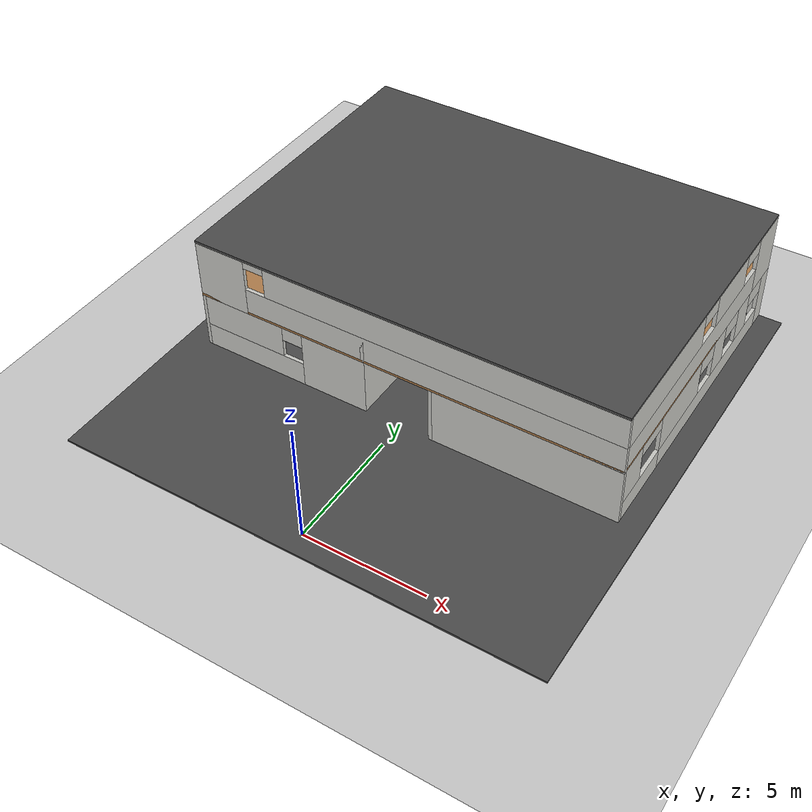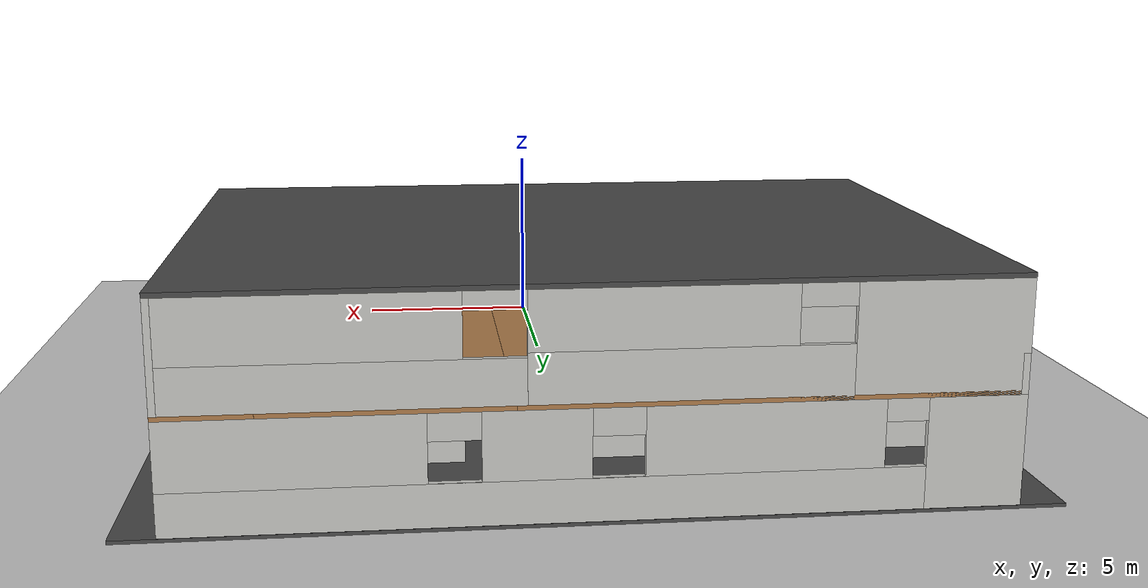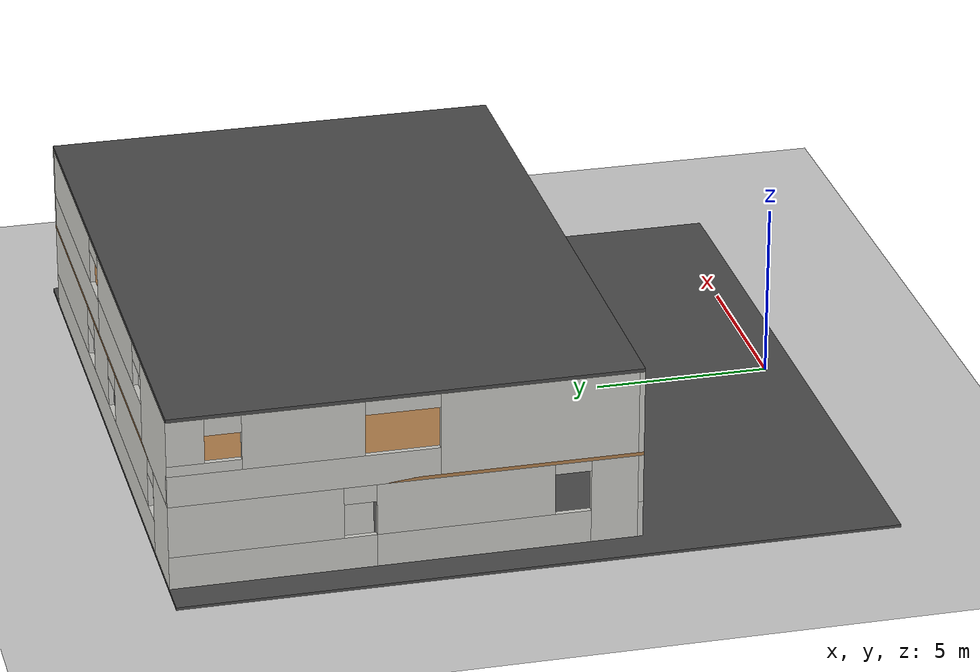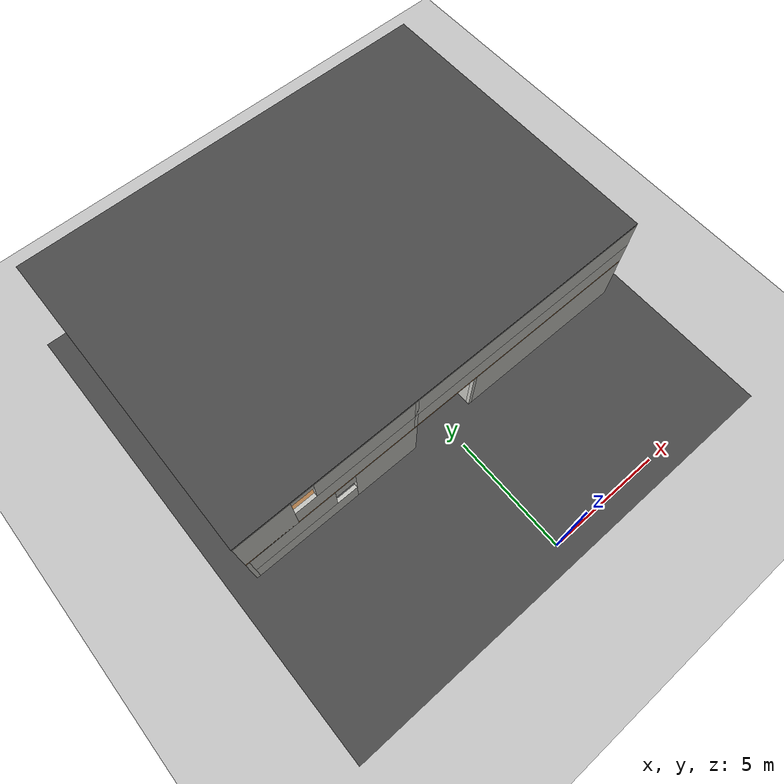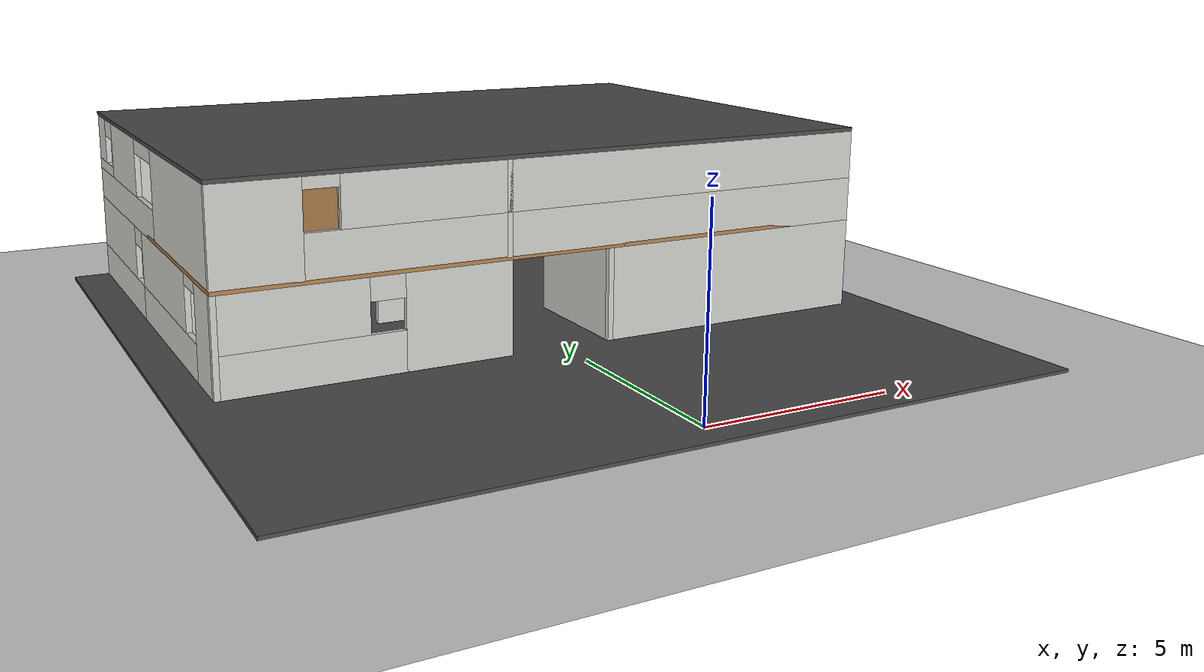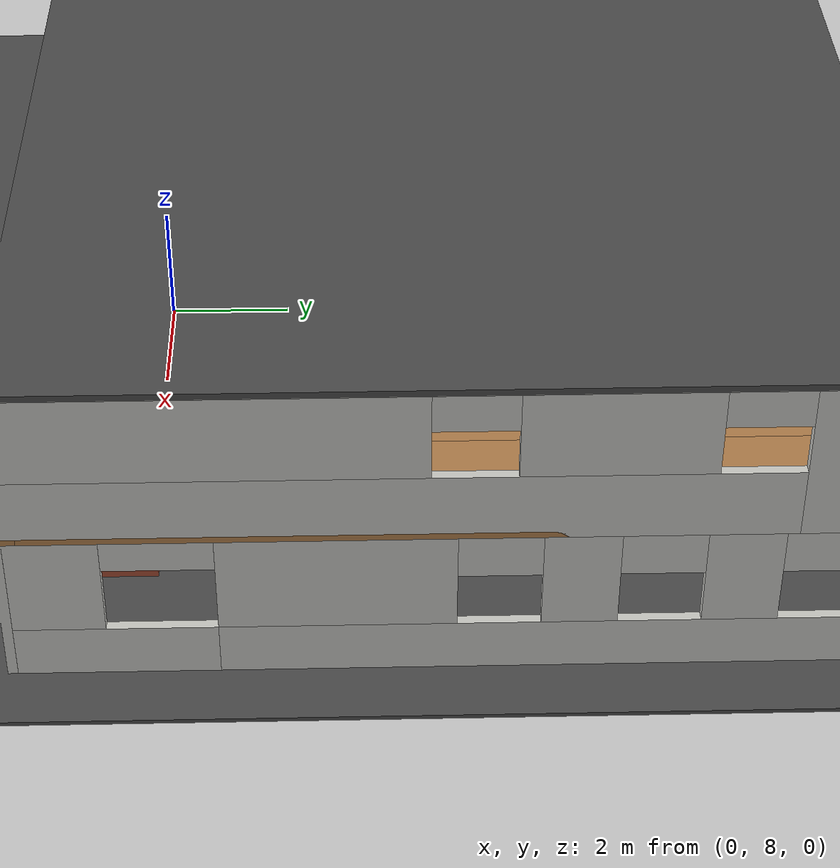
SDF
<sdf version="1.6">
 <world name="default">
  <light name="sun" type="directional">
   <pose>0 0 10 0 -0 0</pose>
   <diffuse>0.8 0.8 0.8 1</diffuse>
   <specular>0.2 0.2 0.2 1</specular>
   <attenuation>
    <range>1000</range>
    <constant>0.9</constant>
    <linear>0.01</linear>
    <quadratic>0.001</quadratic>
   </attenuation>
   <direction>-0.5 0.1 -0.9</direction>
  </light>
  <model name="ground_plane">
   <static>1</static>
   <link name="link">
    <collision name="collision">
     <geometry><plane><normal>0 0 1</normal><size>100 100</size></plane></geometry>
     <surface>
      <contact><collide_bitmask>65535</collide_bitmask></contact>
      <friction><ode><mu>100</mu><mu2>50</mu2></ode></friction>
     </surface>
    </collision>
    <visual name="visual">
     <cast_shadows>0</cast_shadows>
     <geometry><plane><normal>0 0 1</normal><size>100 100</size></plane></geometry>
     <material>
      <script><uri>file://media/materials/scripts/gazebo.material</uri><name>Gazebo/Grey</name></script>
     </material>
    </visual>
   </link>
  </model>
  <gravity>0 0 -9.8</gravity>
  <magnetic_field>6e-06 2.3e-05 -4.2e-05</magnetic_field>
  <atmosphere type="adiabatic"/>
  <physics name="default_physics" default="0" type="ode">
   <max_step_size>0.001</max_step_size>
   <real_time_factor>1</real_time_factor>
   <real_time_update_rate>1000</real_time_update_rate>
  </physics>
  <scene><ambient>0.4 0.4 0.4 1</ambient><background>0.7 0.7 0.7 1</background><shadows>1</shadows></scene>
  <audio><device>default</device></audio>
  <spherical_coordinates>
   <surface_model>EARTH_WGS84</surface_model>
   <latitude_deg>0</latitude_deg>
   <longitude_deg>0</longitude_deg>
   <elevation>0</elevation>
   <heading_deg>0</heading_deg>
  </spherical_coordinates>
  <model name="asphalt_plane">
   <static>1</static>
   <link name="link">
    <collision name="collision"><geometry><box><size>18.0246 12.9845 0.1</size></box></geometry></collision>
    <visual name="visual">
     <cast_shadows>0</cast_shadows>
     <geometry><box><size>18.0246 12.9845 0.1</size></box></geometry>
     <material>
      <script>
       <uri>model://asphalt_plane/materials/scripts</uri>
       <uri>model://asphalt_plane/materials/textures</uri>
       <name>vrc/asphalt</name>
      </script>
     </material>
    </visual>
   </link>
   <pose>0.009253 12.617 5.05625 0 -0 0</pose>
  </model>
  <model name="Indoor_Scenario1">
   <pose>0.016123 12.6195 0 0 -0 0</pose>
   <link name="Floor_0">
    <pose>-0 -0 2.5 0 -0 0</pose>
    <visual name="Floor_0_Visual_0">
     <pose>-3.6411 0 0.05 0 -0 0</pose>
     <geometry><box><size>10.7178 13 0.1</size></box></geometry>
     <material>
      <script><uri>file://media/materials/scripts/gazebo.material</uri><name>Gazebo/Wood</name></script>
      <ambient>1 1 1 1</ambient>
     </material>
     <meta><layer>1</layer></meta>
    </visual>
    <collision name="Floor_0_Collision_0">
     <geometry><box><size>10.7178 13 0.1</size></box></geometry>
     <pose>-3.6411 0 0.05 0 -0 0</pose>
    </collision>
    <visual name="Floor_0_Visual_1">
     <pose>5.3589 -6.32413 0.05 0 -0 0</pose>
     <geometry><box><size>7.2822 0.351742 0.1</size></box></geometry>
     <material>
      <script><uri>file://media/materials/scripts/gazebo.material</uri><name>Gazebo/Wood</name></script>
      <ambient>1 1 1 1</ambient>
     </material>
     <meta><layer>1</layer></meta>
    </visual>
    <collision name="Floor_0_Collision_1">
     <geometry><box><size>7.2822 0.351742 0.1</size></box></geometry>
     <pose>5.3589 -6.32413 0.05 0 -0 0</pose>
    </collision>
    <visual name="Floor_0_Visual_2">
     <pose>7.97998 0.175871 0.05 0 -0 0</pose>
     <geometry><box><size>2.04005 12.6483 0.1</size></box></geometry>
     <material>
      <script><uri>file://media/materials/scripts/gazebo.material</uri><name>Gazebo/Wood</name></script>
      <ambient>1 1 1 1</ambient>
     </material>
     <meta><layer>1</layer></meta>
    </visual>
    <collision name="Floor_0_Collision_2">
     <geometry><box><size>2.04005 12.6483 0.1</size></box></geometry>
     <pose>7.97998 0.175871 0.05 0 -0 0</pose>
    </collision>
    <visual name="Floor_0_Visual_3">
     <pose>4.33888 1.02587 0.05 0 -0 0</pose>
     <geometry><box><size>5.24215 10.9483 0.1</size></box></geometry>
     <material>
      <script><uri>file://media/materials/scripts/gazebo.material</uri><name>Gazebo/Wood</name></script>
      <ambient>1 1 1 1</ambient>
     </material>
     <meta><layer>1</layer></meta>
    </visual>
    <collision name="Floor_0_Collision_3">
     <geometry><box><size>5.24215 10.9483 0.1</size></box></geometry>
     <pose>4.33888 1.02587 0.05 0 -0 0</pose>
    </collision>
   </link>
   <link name="Stairs_0">
    <visual name="Stairs_0_Visual_0">
     <pose>6.78522 -5.29826 0.083333 0 -0 -1.5708</pose>
     <geometry><box><size>1.7 0.349477 0.166667</size></box></geometry>
     <material>
      <script><uri>file://media/materials/scripts/gazebo.material</uri><name>Gazebo/Bricks</name></script>
      <ambient>1 1 1 1</ambient>
     </material>
     <meta><layer>0</layer></meta>
    </visual>
    <collision name="Stairs_0_Collision_0">
     <geometry><box><size>1.7 0.349477 0.166667</size></box></geometry>
     <pose>6.78522 -5.29826 0.083333 0 -0 -1.5708</pose>
    </collision>
    <visual name="Stairs_0_Visual_1">
     <pose>6.43574 -5.29826 0.25 0 -0 -1.5708</pose>
     <geometry><box><size>1.7 0.349477 0.166667</size></box></geometry>
     <material>
      <script><uri>file://media/materials/scripts/gazebo.material</uri><name>Gazebo/Bricks</name></script>
      <ambient>1 1 1 1</ambient>
     </material>
     <meta><layer>0</layer></meta>
    </visual>
    <collision name="Stairs_0_Collision_1">
     <geometry><box><size>1.7 0.349477 0.166667</size></box></geometry>
     <pose>6.43574 -5.29826 0.25 0 -0 -1.5708</pose>
    </collision>
    <visual name="Stairs_0_Visual_2">
     <pose>6.08626 -5.29826 0.416667 0 -0 -1.5708</pose>
     <geometry><box><size>1.7 0.349477 0.166667</size></box></geometry>
     <material>
      <script><uri>file://media/materials/scripts/gazebo.material</uri><name>Gazebo/Bricks</name></script>
      <ambient>1 1 1 1</ambient>
     </material>
     <meta><layer>0</layer></meta>
    </visual>
    <collision name="Stairs_0_Collision_2">
     <geometry><box><size>1.7 0.349477 0.166667</size></box></geometry>
     <pose>6.08626 -5.29826 0.416667 0 -0 -1.5708</pose>
    </collision>
    <visual name="Stairs_0_Visual_3">
     <pose>5.73679 -5.29826 0.583333 0 -0 -1.5708</pose>
     <geometry><box><size>1.7 0.349477 0.166667</size></box></geometry>
     <material>
      <script><uri>file://media/materials/scripts/gazebo.material</uri><name>Gazebo/Bricks</name></script>
      <ambient>1 1 1 1</ambient>
     </material>
     <meta><layer>0</layer></meta>
    </visual>
    <collision name="Stairs_0_Collision_3">
     <geometry><box><size>1.7 0.349477 0.166667</size></box></geometry>
     <pose>5.73679 -5.29826 0.583333 0 -0 -1.5708</pose>
    </collision>
    <visual name="Stairs_0_Visual_4">
     <pose>5.38731 -5.29826 0.75 0 -0 -1.5708</pose>
     <geometry><box><size>1.7 0.349477 0.166667</size></box></geometry>
     <material>
      <script><uri>file://media/materials/scripts/gazebo.material</uri><name>Gazebo/Bricks</name></script>
      <ambient>1 1 1 1</ambient>
     </material>
     <meta><layer>0</layer></meta>
    </visual>
    <collision name="Stairs_0_Collision_4">
     <geometry><box><size>1.7 0.349477 0.166667</size></box></geometry>
     <pose>5.38731 -5.29826 0.75 0 -0 -1.5708</pose>
    </collision>
    <visual name="Stairs_0_Visual_5">
     <pose>5.03783 -5.29826 0.916667 0 -0 -1.5708</pose>
     <geometry><box><size>1.7 0.349477 0.166667</size></box></geometry>
     <material>
      <script><uri>file://media/materials/scripts/gazebo.material</uri><name>Gazebo/Bricks</name></script>
      <ambient>1 1 1 1</ambient>
     </material>
     <meta><layer>0</layer></meta>
    </visual>
    <collision name="Stairs_0_Collision_5">
     <geometry><box><size>1.7 0.349477 0.166667</size></box></geometry>
     <pose>5.03783 -5.29826 0.916667 0 -0 -1.5708</pose>
    </collision>
    <visual name="Stairs_0_Visual_6">
     <pose>4.68835 -5.29826 1.08333 0 -0 -1.5708</pose>
     <geometry><box><size>1.7 0.349477 0.166667</size></box></geometry>
     <material>
      <script><uri>file://media/materials/scripts/gazebo.material</uri><name>Gazebo/Bricks</name></script>
      <ambient>1 1 1 1</ambient>
     </material>
     <meta><layer>0</layer></meta>
    </visual>
    <collision name="Stairs_0_Collision_6">
     <geometry><box><size>1.7 0.349477 0.166667</size></box></geometry>
     <pose>4.68835 -5.29826 1.08333 0 -0 -1.5708</pose>
    </collision>
    <visual name="Stairs_0_Visual_7">
     <pose>4.33888 -5.29826 1.25 0 -0 -1.5708</pose>
     <geometry><box><size>1.7 0.349477 0.166667</size></box></geometry>
     <material>
      <script><uri>file://media/materials/scripts/gazebo.material</uri><name>Gazebo/Bricks</name></script>
      <ambient>1 1 1 1</ambient>
     </material>
     <meta><layer>0</layer></meta>
    </visual>
    <collision name="Stairs_0_Collision_7">
     <geometry><box><size>1.7 0.349477 0.166667</size></box></geometry>
     <pose>4.33888 -5.29826 1.25 0 -0 -1.5708</pose>
    </collision>
    <visual name="Stairs_0_Visual_8">
     <pose>3.9894 -5.29826 1.41667 0 -0 -1.5708</pose>
     <geometry><box><size>1.7 0.349477 0.166667</size></box></geometry>
     <material>
      <script><uri>file://media/materials/scripts/gazebo.material</uri><name>Gazebo/Bricks</name></script>
      <ambient>1 1 1 1</ambient>
     </material>
     <meta><layer>0</layer></meta>
    </visual>
    <collision name="Stairs_0_Collision_8">
     <geometry><box><size>1.7 0.349477 0.166667</size></box></geometry>
     <pose>3.9894 -5.29826 1.41667 0 -0 -1.5708</pose>
    </collision>
    <visual name="Stairs_0_Visual_9">
     <pose>3.63992 -5.29826 1.58333 0 -0 -1.5708</pose>
     <geometry><box><size>1.7 0.349477 0.166667</size></box></geometry>
     <material>
      <script><uri>file://media/materials/scripts/gazebo.material</uri><name>Gazebo/Bricks</name></script>
      <ambient>1 1 1 1</ambient>
     </material>
     <meta><layer>0</layer></meta>
    </visual>
    <collision name="Stairs_0_Collision_9">
     <geometry><box><size>1.7 0.349477 0.166667</size></box></geometry>
     <pose>3.63992 -5.29826 1.58333 0 -0 -1.5708</pose>
    </collision>
    <visual name="Stairs_0_Visual_10">
     <pose>3.29045 -5.29826 1.75 0 -0 -1.5708</pose>
     <geometry><box><size>1.7 0.349477 0.166667</size></box></geometry>
     <material>
      <script><uri>file://media/materials/scripts/gazebo.material</uri><name>Gazebo/Bricks</name></script>
      <ambient>1 1 1 1</ambient>
     </material>
     <meta><layer>0</layer></meta>
    </visual>
    <collision name="Stairs_0_Collision_10">
     <geometry><box><size>1.7 0.349477 0.166667</size></box></geometry>
     <pose>3.29045 -5.29826 1.75 0 -0 -1.5708</pose>
    </collision>
    <visual name="Stairs_0_Visual_11">
     <pose>2.94097 -5.29826 1.91667 0 -0 -1.5708</pose>
     <geometry><box><size>1.7 0.349477 0.166667</size></box></geometry>
     <material>
      <script><uri>file://media/materials/scripts/gazebo.material</uri><name>Gazebo/Bricks</name></script>
      <ambient>1 1 1 1</ambient>
     </material>
     <meta><layer>0</layer></meta>
    </visual>
    <collision name="Stairs_0_Collision_11">
     <geometry><box><size>1.7 0.349477 0.166667</size></box></geometry>
     <pose>2.94097 -5.29826 1.91667 0 -0 -1.5708</pose>
    </collision>
    <visual name="Stairs_0_Visual_12">
     <pose>2.59149 -5.29826 2.08333 0 -0 -1.5708</pose>
     <geometry><box><size>1.7 0.349477 0.166667</size></box></geometry>
     <material>
      <script><uri>file://media/materials/scripts/gazebo.material</uri><name>Gazebo/Bricks</name></script>
      <ambient>1 1 1 1</ambient>
     </material>
     <meta><layer>0</layer></meta>
    </visual>
    <collision name="Stairs_0_Collision_12">
     <geometry><box><size>1.7 0.349477 0.166667</size></box></geometry>
     <pose>2.59149 -5.29826 2.08333 0 -0 -1.5708</pose>
    </collision>
    <visual name="Stairs_0_Visual_13">
     <pose>2.24202 -5.29826 2.25 0 -0 -1.5708</pose>
     <geometry><box><size>1.7 0.349477 0.166667</size></box></geometry>
     <material>
      <script><uri>file://media/materials/scripts/gazebo.material</uri><name>Gazebo/Bricks</name></script>
      <ambient>1 1 1 1</ambient>
     </material>
     <meta><layer>0</layer></meta>
    </visual>
    <collision name="Stairs_0_Collision_13">
     <geometry><box><size>1.7 0.349477 0.166667</size></box></geometry>
     <pose>2.24202 -5.29826 2.25 0 -0 -1.5708</pose>
    </collision>
    <visual name="Stairs_0_Visual_14">
     <pose>1.89254 -5.29826 2.41667 0 -0 -1.5708</pose>
     <geometry><box><size>1.7 0.349477 0.166667</size></box></geometry>
     <material>
      <script><uri>file://media/materials/scripts/gazebo.material</uri><name>Gazebo/Bricks</name></script>
      <ambient>1 1 1 1</ambient>
     </material>
     <meta><layer>0</layer></meta>
    </visual>
    <collision name="Stairs_0_Collision_14">
     <geometry><box><size>1.7 0.349477 0.166667</size></box></geometry>
     <pose>1.89254 -5.29826 2.41667 0 -0 -1.5708</pose>
    </collision>
   </link>
   <link name="Wall_0">
    <pose>-5.25 -6.425 0 0 -0 3.14159</pose>
    <visual name="Wall_0_Visual_0">
     <pose>-2.33577 0 1.25 0 -0 0</pose>
     <geometry><box><size>2.82847 0.15 2.5</size></box></geometry>
     <material>
      <script><uri>file://media/materials/scripts/gazebo.material</uri><name>Gazebo/CeilingTiled</name></script>
      <ambient>0.647059 0.505882 0.309804 1</ambient>
     </material>
     <meta><layer>0</layer></meta>
    </visual>
    <collision name="Wall_0_Collision_0">
     <geometry><box><size>2.82847 0.15 2.5</size></box></geometry>
     <pose>-2.33577 0 1.25 0 -0 0</pose>
    </collision>
    <visual name="Wall_0_Visual_1">
     <pose>1.41423 0 0.55 0 -0 0</pose>
     <geometry><box><size>4.67153 0.15 1.1</size></box></geometry>
     <material>
      <script><uri>file://media/materials/scripts/gazebo.material</uri><name>Gazebo/CeilingTiled</name></script>
      <ambient>0.647059 0.505882 0.309804 1</ambient>
     </material>
     <meta><layer>0</layer></meta>
    </visual>
    <collision name="Wall_0_Collision_1">
     <geometry><box><size>4.67153 0.15 1.1</size></box></geometry>
     <pose>1.41423 0 0.55 0 -0 0</pose>
    </collision>
    <visual name="Wall_0_Visual_2">
     <pose>1.86423 0 1.8 0 -0 0</pose>
     <geometry><box><size>3.77153 0.15 1.4</size></box></geometry>
     <material>
      <script><uri>file://media/materials/scripts/gazebo.material</uri><name>Gazebo/CeilingTiled</name></script>
      <ambient>0.647059 0.505882 0.309804 1</ambient>
     </material>
     <meta><layer>0</layer></meta>
    </visual>
    <collision name="Wall_0_Collision_2">
     <geometry><box><size>3.77153 0.15 1.4</size></box></geometry>
     <pose>1.86423 0 1.8 0 -0 0</pose>
    </collision>
    <visual name="Wall_0_Visual_3">
     <pose>-0.471532 0 2.2 0 -0 0</pose>
     <geometry><box><size>0.9 0.15 0.6</size></box></geometry>
     <material>
      <script><uri>file://media/materials/scripts/gazebo.material</uri><name>Gazebo/CeilingTiled</name></script>
      <ambient>0.647059 0.505882 0.309804 1</ambient>
     </material>
     <meta><layer>0</layer></meta>
    </visual>
    <collision name="Wall_0_Collision_3">
     <geometry><box><size>0.9 0.15 0.6</size></box></geometry>
     <pose>-0.471532 0 2.2 0 -0 0</pose>
    </collision>
   </link>
   <link name="Wall_1">
    <pose>-8.925 -0 0 0 -0 1.5708</pose>
    <visual name="Wall_1_Visual_0">
     <pose>-5.77686 0 1.25 0 -0 0</pose>
     <geometry><box><size>1.44627 0.15 2.5</size></box></geometry>
     <material>
      <script><uri>file://media/materials/scripts/gazebo.material</uri><name>Gazebo/CeilingTiled</name></script>
      <ambient>0.647059 0.505882 0.309804 1</ambient>
     </material>
     <meta><layer>0</layer></meta>
    </visual>
    <collision name="Wall_1_Collision_0">
     <geometry><box><size>1.44627 0.15 2.5</size></box></geometry>
     <pose>-5.77686 0 1.25 0 -0 0</pose>
    </collision>
    <visual name="Wall_1_Visual_1">
     <pose>-2.10736 0 0.5 0 -0 0</pose>
     <geometry><box><size>5.89273 0.15 1</size></box></geometry>
     <material>
      <script><uri>file://media/materials/scripts/gazebo.material</uri><name>Gazebo/CeilingTiled</name></script>
      <ambient>0.647059 0.505882 0.309804 1</ambient>
     </material>
     <meta><layer>0</layer></meta>
    </visual>
    <collision name="Wall_1_Collision_1">
     <geometry><box><size>5.89273 0.15 1</size></box></geometry>
     <pose>-2.10736 0 0.5 0 -0 0</pose>
    </collision>
    <visual name="Wall_1_Visual_2">
     <pose>3.6695 0 0.5 0 -0 0</pose>
     <geometry><box><size>5.66099 0.15 1</size></box></geometry>
     <material>
      <script><uri>file://media/materials/scripts/gazebo.material</uri><name>Gazebo/CeilingTiled</name></script>
      <ambient>0.647059 0.505882 0.309804 1</ambient>
     </material>
     <meta><layer>0</layer></meta>
    </visual>
    <collision name="Wall_1_Collision_2">
     <geometry><box><size>5.66099 0.15 1</size></box></geometry>
     <pose>3.6695 0 0.5 0 -0 0</pose>
    </collision>
    <visual name="Wall_1_Visual_3">
     <pose>4.1195 0 1.75 0 -0 0</pose>
     <geometry><box><size>4.76099 0.15 1.5</size></box></geometry>
     <material>
      <script><uri>file://media/materials/scripts/gazebo.material</uri><name>Gazebo/CeilingTiled</name></script>
      <ambient>0.647059 0.505882 0.309804 1</ambient>
     </material>
     <meta><layer>0</layer></meta>
    </visual>
    <collision name="Wall_1_Collision_3">
     <geometry><box><size>4.76099 0.15 1.5</size></box></geometry>
     <pose>4.1195 0 1.75 0 -0 0</pose>
    </collision>
    <visual name="Wall_1_Visual_4">
     <pose>-1.60736 0 1.75 0 -0 0</pose>
     <geometry><box><size>4.89273 0.15 1.5</size></box></geometry>
     <material>
      <script><uri>file://media/materials/scripts/gazebo.material</uri><name>Gazebo/CeilingTiled</name></script>
      <ambient>0.647059 0.505882 0.309804 1</ambient>
     </material>
     <meta><layer>0</layer></meta>
    </visual>
    <collision name="Wall_1_Collision_4">
     <geometry><box><size>4.89273 0.15 1.5</size></box></geometry>
     <pose>-1.60736 0 1.75 0 -0 0</pose>
    </collision>
    <visual name="Wall_1_Visual_5">
     <pose>-1.60736 0 1.75 0 -0 0</pose>
     <geometry><box><size>4.89273 0.15 1.5</size></box></geometry>
     <material>
      <script><uri>file://media/materials/scripts/gazebo.material</uri><name>Gazebo/CeilingTiled</name></script>
      <ambient>0.647059 0.505882 0.309804 1</ambient>
     </material>
     <meta><layer>0</layer></meta>
    </visual>
    <collision name="Wall_1_Collision_5">
     <geometry><box><size>4.89273 0.15 1.5</size></box></geometry>
     <pose>-1.60736 0 1.75 0 -0 0</pose>
    </collision>
    <visual name="Wall_1_Visual_6">
     <pose>1.28901 0 2.25 0 -0 0</pose>
     <geometry><box><size>0.9 0.15 0.5</size></box></geometry>
     <material>
      <script><uri>file://media/materials/scripts/gazebo.material</uri><name>Gazebo/CeilingTiled</name></script>
      <ambient>0.647059 0.505882 0.309804 1</ambient>
     </material>
     <meta><layer>0</layer></meta>
    </visual>
    <collision name="Wall_1_Collision_6">
     <geometry><box><size>0.9 0.15 0.5</size></box></geometry>
     <pose>1.28901 0 2.25 0 -0 0</pose>
    </collision>
    <visual name="Wall_1_Visual_7">
     <pose>1.28901 0 2.25 0 -0 0</pose>
     <geometry><box><size>0.9 0.15 0.5</size></box></geometry>
     <material>
      <script><uri>file://media/materials/scripts/gazebo.material</uri><name>Gazebo/CeilingTiled</name></script>
      <ambient>0.647059 0.505882 0.309804 1</ambient>
     </material>
     <meta><layer>0</layer></meta>
    </visual>
    <collision name="Wall_1_Collision_7">
     <geometry><box><size>0.9 0.15 0.5</size></box></geometry>
     <pose>1.28901 0 2.25 0 -0 0</pose>
    </collision>
    <visual name="Wall_1_Visual_8">
     <pose>-4.55373 0 2.35 0 -0 0</pose>
     <geometry><box><size>1 0.15 0.3</size></box></geometry>
     <material>
      <script><uri>file://media/materials/scripts/gazebo.material</uri><name>Gazebo/CeilingTiled</name></script>
      <ambient>0.647059 0.505882 0.309804 1</ambient>
     </material>
     <meta><layer>0</layer></meta>
    </visual>
    <collision name="Wall_1_Collision_8">
     <geometry><box><size>1 0.15 0.3</size></box></geometry>
     <pose>-4.55373 0 2.35 0 -0 0</pose>
    </collision>
   </link>
   <link name="Wall_10">
    <collision name="Wall_10_Collision">
     <geometry><box><size>4.25 0.15 2.5</size></box></geometry>
     <pose>0 0 1.25 0 -0 0</pose>
    </collision>
    <visual name="Wall_10_Visual">
     <pose>0 0 1.25 0 -0 0</pose>
     <geometry><box><size>4.25 0.15 2.5</size></box></geometry>
     <material>
      <script><uri>file://media/materials/scripts/gazebo.material</uri><name>Gazebo/CeilingTiled</name></script>
      <ambient>0.647059 0.505882 0.309804 1</ambient>
     </material>
     <meta><layer>0</layer></meta>
    </visual>
    <pose>-1.575 -4.375 0 0 -0 1.5708</pose>
   </link>
   <link name="Wall_101">
    <collision name="Wall_101_Collision">
     <geometry><box><size>0.75 0.15 2.5</size></box></geometry>
     <pose>0 0 1.25 0 -0 0</pose>
    </collision>
    <visual name="Wall_101_Visual">
     <pose>0 0 1.25 0 -0 0</pose>
     <geometry><box><size>0.75 0.15 2.5</size></box></geometry>
     <material>
      <script><uri>file://media/materials/scripts/gazebo.material</uri><name>Gazebo/CeilingTiled</name></script>
      <ambient>1 1 1 1</ambient>
     </material>
     <meta><layer>1</layer></meta>
    </visual>
    <pose>-8.58941 -1.93229 2.5 0 -0 0</pose>
   </link>
   <link name="Wall_102">
    <collision name="Wall_102_Collision">
     <geometry><box><size>0.5 0.15 2.5</size></box></geometry>
     <pose>0 0 1.25 0 -0 0</pose>
    </collision>
    <visual name="Wall_102_Visual">
     <pose>0 0 1.25 0 -0 0</pose>
     <geometry><box><size>0.5 0.15 2.5</size></box></geometry>
     <material>
      <script><uri>file://media/materials/scripts/gazebo.material</uri><name>Gazebo/CeilingTiled</name></script>
      <ambient>1 1 1 1</ambient>
     </material>
     <meta><layer>1</layer></meta>
    </visual>
    <pose>-8.28941 -2.10729 2.5 0 -0 -1.5708</pose>
   </link>
   <link name="Wall_12">
    <collision name="Wall_12_Collision">
     <geometry><box><size>2 0.15 2.5</size></box></geometry>
     <pose>0 0 1.25 0 -0 0</pose>
    </collision>
    <visual name="Wall_12_Visual">
     <pose>0 0 1.25 0 -0 0</pose>
     <geometry><box><size>2 0.15 2.5</size></box></geometry>
     <material>
      <script><uri>file://media/materials/scripts/gazebo.material</uri><name>Gazebo/CeilingTiled</name></script>
      <ambient>1 1 1 1</ambient>
     </material>
     <meta><layer>0</layer></meta>
    </visual>
    <pose>-2.5 -2.325 0 0 -0 3.14159</pose>
   </link>
   <link name="Wall_14">
    <collision name="Wall_14_Collision">
     <geometry><box><size>3.5 0.15 2.5</size></box></geometry>
     <pose>0 0 1.25 0 -0 0</pose>
    </collision>
    <visual name="Wall_14_Visual">
     <pose>0 0 1.25 0 -0 0</pose>
     <geometry><box><size>3.5 0.15 2.5</size></box></geometry>
     <material>
      <script><uri>file://media/materials/scripts/gazebo.material</uri><name>Gazebo/CeilingTiled</name></script>
      <ambient>1 1 1 1</ambient>
     </material>
     <meta><layer>0</layer></meta>
    </visual>
    <pose>-7.19556 -2.34297 0 0 -0 0</pose>
   </link>
   <link name="Wall_19">
    <collision name="Wall_19_Collision">
     <geometry><box><size>0.75 0.15 2.5</size></box></geometry>
     <pose>0 0 1.25 0 -0 0</pose>
    </collision>
    <visual name="Wall_19_Visual">
     <pose>0 0 1.25 0 -0 0</pose>
     <geometry><box><size>0.75 0.15 2.5</size></box></geometry>
     <material>
      <script><uri>file://media/materials/scripts/gazebo.material</uri><name>Gazebo/CeilingTiled</name></script>
      <ambient>1 1 1 1</ambient>
     </material>
     <meta><layer>0</layer></meta>
    </visual>
    <pose>1.67467 -4.10793 0 0 -0 -2.61799</pose>
   </link>
   <link name="Wall_2">
    <pose>-0 6.425 0 0 -0 0</pose>
    <visual name="Wall_2_Visual_0">
     <pose>-7.94017 0 1.25 0 -0 0</pose>
     <geometry><box><size>2.11966 0.15 2.5</size></box></geometry>
     <material>
      <script><uri>file://media/materials/scripts/gazebo.material</uri><name>Gazebo/CeilingTiled</name></script>
      <ambient>0.647059 0.505882 0.309804 1</ambient>
     </material>
     <meta><layer>0</layer></meta>
    </visual>
    <collision name="Wall_2_Collision_0">
     <geometry><box><size>2.11966 0.15 2.5</size></box></geometry>
     <pose>-7.94017 0 1.25 0 -0 0</pose>
    </collision>
    <visual name="Wall_2_Visual_1">
     <pose>1.05983 0 0.5 0 -0 0</pose>
     <geometry><box><size>15.8803 0.15 1</size></box></geometry>
     <material>
      <script><uri>file://media/materials/scripts/gazebo.material</uri><name>Gazebo/CeilingTiled</name></script>
      <ambient>0.647059 0.505882 0.309804 1</ambient>
     </material>
     <meta><layer>0</layer></meta>
    </visual>
    <collision name="Wall_2_Collision_1">
     <geometry><box><size>15.8803 0.15 1</size></box></geometry>
     <pose>1.05983 0 0.5 0 -0 0</pose>
    </collision>
    <visual name="Wall_2_Visual_2">
     <pose>-3.45191 0 1.75 0 -0 0</pose>
     <geometry><box><size>5.05687 0.15 1.5</size></box></geometry>
     <material>
      <script><uri>file://media/materials/scripts/gazebo.material</uri><name>Gazebo/CeilingTiled</name></script>
      <ambient>0.647059 0.505882 0.309804 1</ambient>
     </material>
     <meta><layer>0</layer></meta>
    </visual>
    <collision name="Wall_2_Collision_2">
     <geometry><box><size>5.05687 0.15 1.5</size></box></geometry>
     <pose>-3.45191 0 1.75 0 -0 0</pose>
    </collision>
    <visual name="Wall_2_Visual_3">
     <pose>1.30899 0 1.75 0 -0 0</pose>
     <geometry><box><size>2.26492 0.15 1.5</size></box></geometry>
     <material>
      <script><uri>file://media/materials/scripts/gazebo.material</uri><name>Gazebo/CeilingTiled</name></script>
      <ambient>0.647059 0.505882 0.309804 1</ambient>
     </material>
     <meta><layer>0</layer></meta>
    </visual>
    <collision name="Wall_2_Collision_3">
     <geometry><box><size>2.26492 0.15 1.5</size></box></geometry>
     <pose>1.30899 0 1.75 0 -0 0</pose>
    </collision>
    <visual name="Wall_2_Visual_4">
     <pose>6.27072 0 1.75 0 -0 0</pose>
     <geometry><box><size>5.45855 0.15 1.5</size></box></geometry>
     <material>
      <script><uri>file://media/materials/scripts/gazebo.material</uri><name>Gazebo/CeilingTiled</name></script>
      <ambient>0.647059 0.505882 0.309804 1</ambient>
     </material>
     <meta><layer>0</layer></meta>
    </visual>
    <collision name="Wall_2_Collision_4">
     <geometry><box><size>5.45855 0.15 1.5</size></box></geometry>
     <pose>6.27072 0 1.75 0 -0 0</pose>
    </collision>
    <visual name="Wall_2_Visual_5">
     <pose>-0.373475 0 1 0 -0 0</pose>
     <geometry><box><size>1.1 0.15 0.01</size></box></geometry>
     <material>
      <script><uri>file://media/materials/scripts/gazebo.material</uri><name>Gazebo/CeilingTiled</name></script>
      <ambient>0.647059 0.505882 0.309804 1</ambient>
     </material>
     <meta><layer>0</layer></meta>
    </visual>
    <collision name="Wall_2_Collision_5">
     <geometry><box><size>1.1 0.15 0.01</size></box></geometry>
     <pose>-0.373475 0 1 0 -0 0</pose>
    </collision>
    <visual name="Wall_2_Visual_6">
     <pose>2.99145 0 1 0 -0 0</pose>
     <geometry><box><size>1.1 0.15 0.01</size></box></geometry>
     <material>
      <script><uri>file://media/materials/scripts/gazebo.material</uri><name>Gazebo/CeilingTiled</name></script>
      <ambient>0.647059 0.505882 0.309804 1</ambient>
     </material>
     <meta><layer>0</layer></meta>
    </visual>
    <collision name="Wall_2_Collision_6">
     <geometry><box><size>1.1 0.15 0.01</size></box></geometry>
     <pose>2.99145 0 1 0 -0 0</pose>
    </collision>
    <visual name="Wall_2_Visual_7">
     <pose>-0.373475 0 2.2 0 -0 0</pose>
     <geometry><box><size>1.1 0.15 0.6</size></box></geometry>
     <material>
      <script><uri>file://media/materials/scripts/gazebo.material</uri><name>Gazebo/CeilingTiled</name></script>
      <ambient>0.647059 0.505882 0.309804 1</ambient>
     </material>
     <meta><layer>0</layer></meta>
    </visual>
    <collision name="Wall_2_Collision_7">
     <geometry><box><size>1.1 0.15 0.6</size></box></geometry>
     <pose>-0.373475 0 2.2 0 -0 0</pose>
    </collision>
    <visual name="Wall_2_Visual_8">
     <pose>2.99145 0 2.2 0 -0 0</pose>
     <geometry><box><size>1.1 0.15 0.6</size></box></geometry>
     <material>
      <script><uri>file://media/materials/scripts/gazebo.material</uri><name>Gazebo/CeilingTiled</name></script>
      <ambient>0.647059 0.505882 0.309804 1</ambient>
     </material>
     <meta><layer>0</layer></meta>
    </visual>
    <collision name="Wall_2_Collision_8">
     <geometry><box><size>1.1 0.15 0.6</size></box></geometry>
     <pose>2.99145 0 2.2 0 -0 0</pose>
    </collision>
    <visual name="Wall_2_Visual_9">
     <pose>-6.43034 0 2.25 0 -0 0</pose>
     <geometry><box><size>0.9 0.15 0.5</size></box></geometry>
     <material>
      <script><uri>file://media/materials/scripts/gazebo.material</uri><name>Gazebo/CeilingTiled</name></script>
      <ambient>0.647059 0.505882 0.309804 1</ambient>
     </material>
     <meta><layer>0</layer></meta>
    </visual>
    <collision name="Wall_2_Collision_9">
     <geometry><box><size>0.9 0.15 0.5</size></box></geometry>
     <pose>-6.43034 0 2.25 0 -0 0</pose>
    </collision>
   </link>
   <link name="Wall_23">
    <collision name="Wall_23_Collision">
     <geometry><box><size>4 0.15 2.5</size></box></geometry>
     <pose>0 0 1.25 0 -0 0</pose>
    </collision>
    <visual name="Wall_23_Visual">
     <pose>0 0 1.25 0 -0 0</pose>
     <geometry><box><size>4 0.15 2.5</size></box></geometry>
     <material>
      <script><uri>file://media/materials/scripts/gazebo.material</uri><name>Gazebo/CeilingTiled</name></script>
      <ambient>1 1 1 1</ambient>
     </material>
     <meta><layer>0</layer></meta>
    </visual>
    <pose>-2.14075 4.44918 0 0 -0 -1.5708</pose>
   </link>
   <link name="Wall_24">
    <collision name="Wall_24_Collision">
     <geometry><box><size>1.25 0.15 2.5</size></box></geometry>
     <pose>0 0 1.25 0 -0 0</pose>
    </collision>
    <visual name="Wall_24_Visual">
     <pose>0 0 1.25 0 -0 0</pose>
     <geometry><box><size>1.25 0.15 2.5</size></box></geometry>
     <material>
      <script><uri>file://media/materials/scripts/gazebo.material</uri><name>Gazebo/CeilingTiled</name></script>
      <ambient>1 1 1 1</ambient>
     </material>
     <meta><layer>0</layer></meta>
    </visual>
    <pose>-2.69075 2.52418 0 0 -0 3.14159</pose>
   </link>
   <link name="Wall_28">
    <collision name="Wall_28_Collision">
     <geometry><box><size>4 0.15 2.5</size></box></geometry>
     <pose>0 0 1.25 0 -0 0</pose>
    </collision>
    <visual name="Wall_28_Visual">
     <pose>0 0 1.25 0 -0 0</pose>
     <geometry><box><size>4 0.15 2.5</size></box></geometry>
     <material>
      <script><uri>file://media/materials/scripts/gazebo.material</uri><name>Gazebo/CeilingTiled</name></script>
      <ambient>1 1 1 1</ambient>
     </material>
     <meta><layer>0</layer></meta>
    </visual>
    <pose>-6.98364 2.52637 0 0 -0 0</pose>
   </link>
   <link name="Wall_3">
    <pose>8.925 -0 0 0 -0 -1.5708</pose>
    <visual name="Wall_3_Visual_0">
     <pose>-6.13698 0 1.25 0 -0 0</pose>
     <geometry><box><size>0.726032 0.15 2.5</size></box></geometry>
     <material>
      <script><uri>file://media/materials/scripts/gazebo.material</uri><name>Gazebo/CeilingTiled</name></script>
      <ambient>0.647059 0.505882 0.309804 1</ambient>
     </material>
     <meta><layer>0</layer></meta>
    </visual>
    <collision name="Wall_3_Collision_0">
     <geometry><box><size>0.726032 0.15 2.5</size></box></geometry>
     <pose>-6.13698 0 1.25 0 -0 0</pose>
    </collision>
    <visual name="Wall_3_Visual_1">
     <pose>-1.17837 0 0.45 0 -0 0</pose>
     <geometry><box><size>9.1912 0.15 0.9</size></box></geometry>
     <material>
      <script><uri>file://media/materials/scripts/gazebo.material</uri><name>Gazebo/CeilingTiled</name></script>
      <ambient>0.647059 0.505882 0.309804 1</ambient>
     </material>
     <meta><layer>0</layer></meta>
    </visual>
    <collision name="Wall_3_Collision_1">
     <geometry><box><size>9.1912 0.15 0.9</size></box></geometry>
     <pose>-1.17837 0 0.45 0 -0 0</pose>
    </collision>
    <visual name="Wall_3_Visual_2">
     <pose>4.95862 0 0.45 0 -0 0</pose>
     <geometry><box><size>3.08277 0.15 0.9</size></box></geometry>
     <material>
      <script><uri>file://media/materials/scripts/gazebo.material</uri><name>Gazebo/CeilingTiled</name></script>
      <ambient>0.647059 0.505882 0.309804 1</ambient>
     </material>
     <meta><layer>0</layer></meta>
    </visual>
    <collision name="Wall_3_Collision_2">
     <geometry><box><size>3.08277 0.15 0.9</size></box></geometry>
     <pose>4.95862 0 0.45 0 -0 0</pose>
    </collision>
    <visual name="Wall_3_Visual_3">
     <pose>5.75862 0 1.7 0 -0 0</pose>
     <geometry><box><size>1.48277 0.15 1.6</size></box></geometry>
     <material>
      <script><uri>file://media/materials/scripts/gazebo.material</uri><name>Gazebo/CeilingTiled</name></script>
      <ambient>0.647059 0.505882 0.309804 1</ambient>
     </material>
     <meta><layer>0</layer></meta>
    </visual>
    <collision name="Wall_3_Collision_3">
     <geometry><box><size>1.48277 0.15 1.6</size></box></geometry>
     <pose>5.75862 0 1.7 0 -0 0</pose>
    </collision>
    <visual name="Wall_3_Visual_4">
     <pose>-4.02683 0 1.7 0 -0 0</pose>
     <geometry><box><size>1.09427 0.15 1.6</size></box></geometry>
     <material>
      <script><uri>file://media/materials/scripts/gazebo.material</uri><name>Gazebo/CeilingTiled</name></script>
      <ambient>0.647059 0.505882 0.309804 1</ambient>
     </material>
     <meta><layer>0</layer></meta>
    </visual>
    <collision name="Wall_3_Collision_4">
     <geometry><box><size>1.09427 0.15 1.6</size></box></geometry>
     <pose>-4.02683 0 1.7 0 -0 0</pose>
    </collision>
    <visual name="Wall_3_Visual_5">
     <pose>-1.73257 0 1.7 0 -0 0</pose>
     <geometry><box><size>1.09427 0.15 1.6</size></box></geometry>
     <material>
      <script><uri>file://media/materials/scripts/gazebo.material</uri><name>Gazebo/CeilingTiled</name></script>
      <ambient>0.647059 0.505882 0.309804 1</ambient>
     </material>
     <meta><layer>0</layer></meta>
    </visual>
    <collision name="Wall_3_Collision_5">
     <geometry><box><size>1.09427 0.15 1.6</size></box></geometry>
     <pose>-1.73257 0 1.7 0 -0 0</pose>
    </collision>
    <visual name="Wall_3_Visual_6">
     <pose>1.7159 0 1.7 0 -0 0</pose>
     <geometry><box><size>3.40267 0.15 1.6</size></box></geometry>
     <material>
      <script><uri>file://media/materials/scripts/gazebo.material</uri><name>Gazebo/CeilingTiled</name></script>
      <ambient>0.647059 0.505882 0.309804 1</ambient>
     </material>
     <meta><layer>0</layer></meta>
    </visual>
    <collision name="Wall_3_Collision_6">
     <geometry><box><size>3.40267 0.15 1.6</size></box></geometry>
     <pose>1.7159 0 1.7 0 -0 0</pose>
    </collision>
    <visual name="Wall_3_Visual_7">
     <pose>1.7159 0 1.7 0 -0 0</pose>
     <geometry><box><size>3.40267 0.15 1.6</size></box></geometry>
     <material>
      <script><uri>file://media/materials/scripts/gazebo.material</uri><name>Gazebo/CeilingTiled</name></script>
      <ambient>0.647059 0.505882 0.309804 1</ambient>
     </material>
     <meta><layer>0</layer></meta>
    </visual>
    <collision name="Wall_3_Collision_7">
     <geometry><box><size>3.40267 0.15 1.6</size></box></geometry>
     <pose>1.7159 0 1.7 0 -0 0</pose>
    </collision>
    <visual name="Wall_3_Visual_8">
     <pose>-5.17397 0 2.15 0 -0 0</pose>
     <geometry><box><size>1.2 0.15 0.7</size></box></geometry>
     <material>
      <script><uri>file://media/materials/scripts/gazebo.material</uri><name>Gazebo/CeilingTiled</name></script>
      <ambient>0.647059 0.505882 0.309804 1</ambient>
     </material>
     <meta><layer>0</layer></meta>
    </visual>
    <collision name="Wall_3_Collision_8">
     <geometry><box><size>1.2 0.15 0.7</size></box></geometry>
     <pose>-5.17397 0 2.15 0 -0 0</pose>
    </collision>
    <visual name="Wall_3_Visual_9">
     <pose>-2.8797 0 2.15 0 -0 0</pose>
     <geometry><box><size>1.2 0.15 0.7</size></box></geometry>
     <material>
      <script><uri>file://media/materials/scripts/gazebo.material</uri><name>Gazebo/CeilingTiled</name></script>
      <ambient>0.647059 0.505882 0.309804 1</ambient>
     </material>
     <meta><layer>0</layer></meta>
    </visual>
    <collision name="Wall_3_Collision_9">
     <geometry><box><size>1.2 0.15 0.7</size></box></geometry>
     <pose>-2.8797 0 2.15 0 -0 0</pose>
    </collision>
    <visual name="Wall_3_Visual_10">
     <pose>-0.585434 0 2.15 0 -0 0</pose>
     <geometry><box><size>1.2 0.15 0.7</size></box></geometry>
     <material>
      <script><uri>file://media/materials/scripts/gazebo.material</uri><name>Gazebo/CeilingTiled</name></script>
      <ambient>0.647059 0.505882 0.309804 1</ambient>
     </material>
     <meta><layer>0</layer></meta>
    </visual>
    <collision name="Wall_3_Collision_10">
     <geometry><box><size>1.2 0.15 0.7</size></box></geometry>
     <pose>-0.585434 0 2.15 0 -0 0</pose>
    </collision>
    <visual name="Wall_3_Visual_11">
     <pose>4.21723 0 2.25 0 -0 0</pose>
     <geometry><box><size>1.6 0.15 0.5</size></box></geometry>
     <material>
      <script><uri>file://media/materials/scripts/gazebo.material</uri><name>Gazebo/CeilingTiled</name></script>
      <ambient>0.647059 0.505882 0.309804 1</ambient>
     </material>
     <meta><layer>0</layer></meta>
    </visual>
    <collision name="Wall_3_Collision_11">
     <geometry><box><size>1.6 0.15 0.5</size></box></geometry>
     <pose>4.21723 0 2.25 0 -0 0</pose>
    </collision>
    <visual name="Wall_3_Visual_12">
     <pose>4.21723 0 2.25 0 -0 0</pose>
     <geometry><box><size>1.6 0.15 0.5</size></box></geometry>
     <material>
      <script><uri>file://media/materials/scripts/gazebo.material</uri><name>Gazebo/CeilingTiled</name></script>
      <ambient>0.647059 0.505882 0.309804 1</ambient>
     </material>
     <meta><layer>0</layer></meta>
    </visual>
    <collision name="Wall_3_Collision_12">
     <geometry><box><size>1.6 0.15 0.5</size></box></geometry>
     <pose>4.21723 0 2.25 0 -0 0</pose>
    </collision>
   </link>
   <link name="Wall_31">
    <collision name="Wall_31_Collision">
     <geometry><box><size>2 0.15 2.5</size></box></geometry>
     <pose>0 0 1.25 0 -0 0</pose>
    </collision>
    <visual name="Wall_31_Visual">
     <pose>0 0 1.25 0 -0 0</pose>
     <geometry><box><size>2 0.15 2.5</size></box></geometry>
     <material>
      <script><uri>file://media/materials/scripts/gazebo.material</uri><name>Gazebo/CeilingTiled</name></script>
      <ambient>1 1 1 1</ambient>
     </material>
     <meta><layer>0</layer></meta>
    </visual>
    <pose>-7.19005 1.55574 0 0 -0 -1.5708</pose>
   </link>
   <link name="Wall_33">
    <collision name="Wall_33_Collision">
     <geometry><box><size>1.5 0.15 2.5</size></box></geometry>
     <pose>0 0 1.25 0 -0 0</pose>
    </collision>
    <visual name="Wall_33_Visual">
     <pose>0 0 1.25 0 -0 0</pose>
     <geometry><box><size>1.5 0.15 2.5</size></box></geometry>
     <material>
      <script><uri>file://media/materials/scripts/gazebo.material</uri><name>Gazebo/CeilingTiled</name></script>
      <ambient>1 1 1 1</ambient>
     </material>
     <meta><layer>0</layer></meta>
    </visual>
    <pose>-7.22047 -1.63502 0 0 -0 1.5708</pose>
   </link>
   <link name="Wall_35">
    <collision name="Wall_35_Collision">
     <geometry><box><size>3 0.15 2.5</size></box></geometry>
     <pose>0 0 1.25 0 -0 0</pose>
    </collision>
    <visual name="Wall_35_Visual">
     <pose>0 0 1.25 0 -0 0</pose>
     <geometry><box><size>3 0.15 2.5</size></box></geometry>
     <material>
      <script><uri>file://media/materials/scripts/gazebo.material</uri><name>Gazebo/CeilingTiled</name></script>
      <ambient>1 1 1 1</ambient>
     </material>
     <meta><layer>0</layer></meta>
    </visual>
    <pose>-0.715749 2.52418 0 0 -0 0</pose>
   </link>
   <link name="Wall_37">
    <collision name="Wall_37_Collision">
     <geometry><box><size>4 0.15 2.5</size></box></geometry>
     <pose>0 0 1.25 0 -0 0</pose>
    </collision>
    <visual name="Wall_37_Visual">
     <pose>0 0 1.25 0 -0 0</pose>
     <geometry><box><size>4 0.15 2.5</size></box></geometry>
     <material>
      <script><uri>file://media/materials/scripts/gazebo.material</uri><name>Gazebo/CeilingTiled</name></script>
      <ambient>1 1 1 1</ambient>
     </material>
     <meta><layer>0</layer></meta>
    </visual>
    <pose>4.54502 4.4469 0 0 -0 -1.5708</pose>
   </link>
   <link name="Wall_38">
    <collision name="Wall_38_Collision">
     <geometry><box><size>2 0.15 2.5</size></box></geometry>
     <pose>0 0 1.25 0 -0 0</pose>
    </collision>
    <visual name="Wall_38_Visual">
     <pose>0 0 1.25 0 -0 0</pose>
     <geometry><box><size>2 0.15 2.5</size></box></geometry>
     <material>
      <script><uri>file://media/materials/scripts/gazebo.material</uri><name>Gazebo/CeilingTiled</name></script>
      <ambient>1 1 1 1</ambient>
     </material>
     <meta><layer>0</layer></meta>
    </visual>
    <pose>3.62002 2.50441 0 0 -0 3.14159</pose>
   </link>
   <link name="Wall_4">
    <collision name="Wall_4_Collision">
     <geometry><box><size>7.75 0.15 2.5</size></box></geometry>
     <pose>0 0 1.25 0 -0 0</pose>
    </collision>
    <visual name="Wall_4_Visual">
     <pose>0 0 1.25 0 -0 0</pose>
     <geometry><box><size>7.75 0.15 2.5</size></box></geometry>
     <material>
      <script><uri>file://media/materials/scripts/gazebo.material</uri><name>Gazebo/CeilingTiled</name></script>
      <ambient>0.647059 0.505882 0.309804 1</ambient>
     </material>
     <meta><layer>0</layer></meta>
    </visual>
    <pose>5.125 -6.425 0 0 -0 3.14159</pose>
   </link>
   <link name="Wall_40">
    <collision name="Wall_40_Collision">
     <geometry><box><size>1.25 0.15 2.5</size></box></geometry>
     <pose>0 0 1.25 0 -0 0</pose>
    </collision>
    <visual name="Wall_40_Visual">
     <pose>0 0 1.25 0 -0 0</pose>
     <geometry><box><size>1.25 0.15 2.5</size></box></geometry>
     <material>
      <script><uri>file://media/materials/scripts/gazebo.material</uri><name>Gazebo/CeilingTiled</name></script>
      <ambient>1 1 1 1</ambient>
     </material>
     <meta><layer>0</layer></meta>
    </visual>
    <pose>4.54502 1.95441 0 0 -0 -1.5708</pose>
   </link>
   <link name="Wall_42">
    <collision name="Wall_42_Collision">
     <geometry><box><size>4.5 0.15 2.5</size></box></geometry>
     <pose>0 0 1.25 0 -0 0</pose>
    </collision>
    <visual name="Wall_42_Visual">
     <pose>0 0 1.25 0 -0 0</pose>
     <geometry><box><size>4.5 0.15 2.5</size></box></geometry>
     <material>
      <script><uri>file://media/materials/scripts/gazebo.material</uri><name>Gazebo/CeilingTiled</name></script>
      <ambient>1 1 1 1</ambient>
     </material>
     <meta><layer>0</layer></meta>
    </visual>
    <pose>6.74627 -0.890762 0 0 -0 3.14159</pose>
   </link>
   <link name="Wall_43">
    <collision name="Wall_43_Collision">
     <geometry><box><size>0.75 0.15 2.5</size></box></geometry>
     <pose>0 0 1.25 0 -0 0</pose>
    </collision>
    <visual name="Wall_43_Visual">
     <pose>0 0 1.25 0 -0 0</pose>
     <geometry><box><size>0.75 0.15 2.5</size></box></geometry>
     <material>
      <script><uri>file://media/materials/scripts/gazebo.material</uri><name>Gazebo/CeilingTiled</name></script>
      <ambient>1 1 1 1</ambient>
     </material>
     <meta><layer>0</layer></meta>
    </visual>
    <pose>4.57127 -0.590762 0 0 -0 1.5708</pose>
   </link>
   <link name="Wall_46">
    <collision name="Wall_46_Collision">
     <geometry><box><size>1 0.15 2.5</size></box></geometry>
     <pose>0 0 1.25 0 -0 0</pose>
    </collision>
    <visual name="Wall_46_Visual">
     <pose>0 0 1.25 0 -0 0</pose>
     <geometry><box><size>1 0.15 2.5</size></box></geometry>
     <material>
      <script><uri>file://media/materials/scripts/gazebo.material</uri><name>Gazebo/CeilingTiled</name></script>
      <ambient>1 1 1 1</ambient>
     </material>
     <meta><layer>0</layer></meta>
    </visual>
    <pose>8.59215 -1.24375 0 0 -0 -0.785398</pose>
   </link>
   <link name="Wall_48">
    <collision name="Wall_48_Collision">
     <geometry><box><size>0.75 0.15 2.5</size></box></geometry>
     <pose>0 0 1.25 0 -0 0</pose>
    </collision>
    <visual name="Wall_48_Visual">
     <pose>0 0 1.25 0 -0 0</pose>
     <geometry><box><size>0.75 0.15 2.5</size></box></geometry>
     <material>
      <script><uri>file://media/materials/scripts/gazebo.material</uri><name>Gazebo/CeilingTiled</name></script>
      <ambient>1 1 1 1</ambient>
     </material>
     <meta><layer>0</layer></meta>
    </visual>
    <pose>4.28416 2.24221 0 0 -0 2.35619</pose>
   </link>
   <link name="Wall_5">
    <collision name="Wall_5_Collision">
     <geometry><box><size>3.5 0.15 2.5</size></box></geometry>
     <pose>0 0 1.25 0 -0 0</pose>
    </collision>
    <visual name="Wall_5_Visual">
     <pose>0 0 1.25 0 -0 0</pose>
     <geometry><box><size>3.5 0.15 2.5</size></box></geometry>
     <material>
      <script><uri>file://media/materials/scripts/gazebo.material</uri><name>Gazebo/CeilingTiled</name></script>
      <ambient>0.647059 0.505882 0.309804 1</ambient>
     </material>
     <meta><layer>0</layer></meta>
    </visual>
    <pose>1.325 -4.75 0 0 -0 1.5708</pose>
   </link>
   <link name="Wall_50">
    <collision name="Wall_50_Collision">
     <geometry><box><size>0.75 0.15 2.5</size></box></geometry>
     <pose>0 0 1.25 0 -0 0</pose>
    </collision>
    <visual name="Wall_50_Visual">
     <pose>0 0 1.25 0 -0 0</pose>
     <geometry><box><size>0.75 0.15 2.5</size></box></geometry>
     <material>
      <script><uri>file://media/materials/scripts/gazebo.material</uri><name>Gazebo/CeilingTiled</name></script>
      <ambient>1 1 1 1</ambient>
     </material>
     <meta><layer>0</layer></meta>
    </visual>
    <pose>-6.87479 2.33749 0 0 -0 0.523599</pose>
   </link>
   <link name="Wall_52">
    <collision name="Wall_52_Collision">
     <geometry><box><size>0.75 0.15 2.5</size></box></geometry>
     <pose>0 0 1.25 0 -0 0</pose>
    </collision>
    <visual name="Wall_52_Visual">
     <pose>0 0 1.25 0 -0 0</pose>
     <geometry><box><size>0.75 0.15 2.5</size></box></geometry>
     <material>
      <script><uri>file://media/materials/scripts/gazebo.material</uri><name>Gazebo/CeilingTiled</name></script>
      <ambient>1 1 1 1</ambient>
     </material>
     <meta><layer>0</layer></meta>
    </visual>
    <pose>-6.90469 -2.13997 0 0 -0 2.61799</pose>
   </link>
   <link name="Wall_55">
    <pose>-8.925 -0 2.5 0 -0 1.5708</pose>
    <visual name="Wall_55_Visual_0">
     <pose>-3.7021 0 1.25 0 -0 0</pose>
     <geometry><box><size>5.59579 0.15 2.5</size></box></geometry>
     <material>
      <script><uri>file://media/materials/scripts/gazebo.material</uri><name>Gazebo/CeilingTiled</name></script>
      <ambient>0.647059 0.505882 0.305882 1</ambient>
     </material>
     <meta><layer>1</layer></meta>
    </visual>
    <collision name="Wall_55_Collision_0">
     <geometry><box><size>5.59579 0.15 2.5</size></box></geometry>
     <pose>-3.7021 0 1.25 0 -0 0</pose>
    </collision>
    <visual name="Wall_55_Visual_1">
     <pose>2.7979 0 0.45 0 -0 0</pose>
     <geometry><box><size>7.40421 0.15 0.9</size></box></geometry>
     <material>
      <script><uri>file://media/materials/scripts/gazebo.material</uri><name>Gazebo/CeilingTiled</name></script>
      <ambient>0.647059 0.505882 0.305882 1</ambient>
     </material>
     <meta><layer>1</layer></meta>
    </visual>
    <collision name="Wall_55_Collision_1">
     <geometry><box><size>7.40421 0.15 0.9</size></box></geometry>
     <pose>2.7979 0 0.45 0 -0 0</pose>
    </collision>
    <visual name="Wall_55_Visual_2">
     <pose>2.80473 0 1.7 0 -0 0</pose>
     <geometry><box><size>3.32387 0.15 1.6</size></box></geometry>
     <material>
      <script><uri>file://media/materials/scripts/gazebo.material</uri><name>Gazebo/CeilingTiled</name></script>
      <ambient>0.647059 0.505882 0.305882 1</ambient>
     </material>
     <meta><layer>1</layer></meta>
    </visual>
    <collision name="Wall_55_Collision_2">
     <geometry><box><size>3.32387 0.15 1.6</size></box></geometry>
     <pose>2.80473 0 1.7 0 -0 0</pose>
    </collision>
    <visual name="Wall_55_Visual_3">
     <pose>5.48333 0 1.05 0 -0 0</pose>
     <geometry><box><size>2.03333 0.15 0.3</size></box></geometry>
     <material>
      <script><uri>file://media/materials/scripts/gazebo.material</uri><name>Gazebo/CeilingTiled</name></script>
      <ambient>0.647059 0.505882 0.305882 1</ambient>
     </material>
     <meta><layer>1</layer></meta>
    </visual>
    <collision name="Wall_55_Collision_3">
     <geometry><box><size>2.03333 0.15 0.3</size></box></geometry>
     <pose>5.48333 0 1.05 0 -0 0</pose>
    </collision>
    <visual name="Wall_55_Visual_4">
     <pose>5.98333 0 1.85 0 -0 0</pose>
     <geometry><box><size>1.03333 0.15 1.3</size></box></geometry>
     <material>
      <script><uri>file://media/materials/scripts/gazebo.material</uri><name>Gazebo/CeilingTiled</name></script>
      <ambient>0.647059 0.505882 0.305882 1</ambient>
     </material>
     <meta><layer>1</layer></meta>
    </visual>
    <collision name="Wall_55_Collision_4">
     <geometry><box><size>1.03333 0.15 1.3</size></box></geometry>
     <pose>5.98333 0 1.85 0 -0 0</pose>
    </collision>
    <visual name="Wall_55_Visual_5">
     <pose>4.96667 0 2.25 0 -0 0</pose>
     <geometry><box><size>1 0.15 0.5</size></box></geometry>
     <material>
      <script><uri>file://media/materials/scripts/gazebo.material</uri><name>Gazebo/CeilingTiled</name></script>
      <ambient>0.647059 0.505882 0.305882 1</ambient>
     </material>
     <meta><layer>1</layer></meta>
    </visual>
    <collision name="Wall_55_Collision_5">
     <geometry><box><size>1 0.15 0.5</size></box></geometry>
     <pose>4.96667 0 2.25 0 -0 0</pose>
    </collision>
    <visual name="Wall_55_Visual_6">
     <pose>0.119295 0 2.3 0 -0 0</pose>
     <geometry><box><size>2.047 0.15 0.4</size></box></geometry>
     <material>
      <script><uri>file://media/materials/scripts/gazebo.material</uri><name>Gazebo/CeilingTiled</name></script>
      <ambient>0.647059 0.505882 0.305882 1</ambient>
     </material>
     <meta><layer>1</layer></meta>
    </visual>
    <collision name="Wall_55_Collision_6">
     <geometry><box><size>2.047 0.15 0.4</size></box></geometry>
     <pose>0.119295 0 2.3 0 -0 0</pose>
    </collision>
   </link>
   <link name="Wall_56">
    <pose>-0 6.425 2.5 0 -0 0</pose>
    <visual name="Wall_56_Visual_0">
     <pose>-7.13278 0 1.25 0 -0 0</pose>
     <geometry><box><size>3.73445 0.15 2.5</size></box></geometry>
     <material>
      <script><uri>file://media/materials/scripts/gazebo.material</uri><name>Gazebo/CeilingTiled</name></script>
      <ambient>0.647059 0.505882 0.305882 1</ambient>
     </material>
     <meta><layer>1</layer></meta>
    </visual>
    <collision name="Wall_56_Collision_0">
     <geometry><box><size>3.73445 0.15 2.5</size></box></geometry>
     <pose>-7.13278 0 1.25 0 -0 0</pose>
    </collision>
    <visual name="Wall_56_Visual_1">
     <pose>-1.88131 0 0.6 0 -0 0</pose>
     <geometry><box><size>6.7685 0.15 1.2</size></box></geometry>
     <material>
      <script><uri>file://media/materials/scripts/gazebo.material</uri><name>Gazebo/CeilingTiled</name></script>
      <ambient>0.647059 0.505882 0.305882 1</ambient>
     </material>
     <meta><layer>1</layer></meta>
    </visual>
    <collision name="Wall_56_Collision_1">
     <geometry><box><size>6.7685 0.15 1.2</size></box></geometry>
     <pose>-1.88131 0 0.6 0 -0 0</pose>
    </collision>
    <visual name="Wall_56_Visual_2">
     <pose>5.25147 0 0.55 0 -0 0</pose>
     <geometry><box><size>7.49705 0.15 1.1</size></box></geometry>
     <material>
      <script><uri>file://media/materials/scripts/gazebo.material</uri><name>Gazebo/CeilingTiled</name></script>
      <ambient>0.647059 0.505882 0.305882 1</ambient>
     </material>
     <meta><layer>1</layer></meta>
    </visual>
    <collision name="Wall_56_Collision_2">
     <geometry><box><size>7.49705 0.15 1.1</size></box></geometry>
     <pose>5.25147 0 0.55 0 -0 0</pose>
    </collision>
    <visual name="Wall_56_Visual_3">
     <pose>5.90147 0 1.8 0 -0 0</pose>
     <geometry><box><size>6.19705 0.15 1.4</size></box></geometry>
     <material>
      <script><uri>file://media/materials/scripts/gazebo.material</uri><name>Gazebo/CeilingTiled</name></script>
      <ambient>0.647059 0.505882 0.305882 1</ambient>
     </material>
     <meta><layer>1</layer></meta>
    </visual>
    <collision name="Wall_56_Collision_3">
     <geometry><box><size>6.19705 0.15 1.4</size></box></geometry>
     <pose>5.90147 0 1.8 0 -0 0</pose>
    </collision>
    <visual name="Wall_56_Visual_4">
     <pose>-1.2813 0 1.85 0 -0 0</pose>
     <geometry><box><size>5.5685 0.15 1.3</size></box></geometry>
     <material>
      <script><uri>file://media/materials/scripts/gazebo.material</uri><name>Gazebo/CeilingTiled</name></script>
      <ambient>0.647059 0.505882 0.305882 1</ambient>
     </material>
     <meta><layer>1</layer></meta>
    </visual>
    <collision name="Wall_56_Collision_4">
     <geometry><box><size>5.5685 0.15 1.3</size></box></geometry>
     <pose>-1.2813 0 1.85 0 -0 0</pose>
    </collision>
    <visual name="Wall_56_Visual_5">
     <pose>-4.66556 0 2.25 0 -0 0</pose>
     <geometry><box><size>1.2 0.15 0.5</size></box></geometry>
     <material>
      <script><uri>file://media/materials/scripts/gazebo.material</uri><name>Gazebo/CeilingTiled</name></script>
      <ambient>0.647059 0.505882 0.305882 1</ambient>
     </material>
     <meta><layer>1</layer></meta>
    </visual>
    <collision name="Wall_56_Collision_5">
     <geometry><box><size>1.2 0.15 0.5</size></box></geometry>
     <pose>-4.66556 0 2.25 0 -0 0</pose>
    </collision>
    <visual name="Wall_56_Visual_6">
     <pose>2.15295 0 2.3 0 -0 0</pose>
     <geometry><box><size>1.3 0.15 0.4</size></box></geometry>
     <material>
      <script><uri>file://media/materials/scripts/gazebo.material</uri><name>Gazebo/CeilingTiled</name></script>
      <ambient>0.647059 0.505882 0.305882 1</ambient>
     </material>
     <meta><layer>1</layer></meta>
    </visual>
    <collision name="Wall_56_Collision_6">
     <geometry><box><size>1.3 0.15 0.4</size></box></geometry>
     <pose>2.15295 0 2.3 0 -0 0</pose>
    </collision>
   </link>
   <link name="Wall_57">
    <pose>8.925 -0 2.5 0 -0 -1.5708</pose>
    <visual name="Wall_57_Visual_0">
     <pose>-5.62101 0 1.25 0 -0 0</pose>
     <geometry><box><size>1.75799 0.15 2.5</size></box></geometry>
     <material>
      <script><uri>file://media/materials/scripts/gazebo.material</uri><name>Gazebo/CeilingTiled</name></script>
      <ambient>0.647059 0.505882 0.305882 1</ambient>
     </material>
     <meta><layer>1</layer></meta>
    </visual>
    <collision name="Wall_57_Collision_0">
     <geometry><box><size>1.75799 0.15 2.5</size></box></geometry>
     <pose>-5.62101 0 1.25 0 -0 0</pose>
    </collision>
    <visual name="Wall_57_Visual_1">
     <pose>0.878995 0 0.55 0 -0 0</pose>
     <geometry><box><size>11.242 0.15 1.1</size></box></geometry>
     <material>
      <script><uri>file://media/materials/scripts/gazebo.material</uri><name>Gazebo/CeilingTiled</name></script>
      <ambient>0.647059 0.505882 0.305882 1</ambient>
     </material>
     <meta><layer>1</layer></meta>
    </visual>
    <collision name="Wall_57_Collision_1">
     <geometry><box><size>11.242 0.15 1.1</size></box></geometry>
     <pose>0.878995 0 0.55 0 -0 0</pose>
    </collision>
    <visual name="Wall_57_Visual_2">
     <pose>-2.17088 0 1.8 0 -0 0</pose>
     <geometry><box><size>2.74226 0.15 1.4</size></box></geometry>
     <material>
      <script><uri>file://media/materials/scripts/gazebo.material</uri><name>Gazebo/CeilingTiled</name></script>
      <ambient>0.647059 0.505882 0.305882 1</ambient>
     </material>
     <meta><layer>1</layer></meta>
    </visual>
    <collision name="Wall_57_Collision_2">
     <geometry><box><size>2.74226 0.15 1.4</size></box></geometry>
     <pose>-2.17088 0 1.8 0 -0 0</pose>
    </collision>
    <visual name="Wall_57_Visual_3">
     <pose>3.45012 0 1.8 0 -0 0</pose>
     <geometry><box><size>6.09975 0.15 1.4</size></box></geometry>
     <material>
      <script><uri>file://media/materials/scripts/gazebo.material</uri><name>Gazebo/CeilingTiled</name></script>
      <ambient>0.647059 0.505882 0.305882 1</ambient>
     </material>
     <meta><layer>1</layer></meta>
    </visual>
    <collision name="Wall_57_Collision_3">
     <geometry><box><size>6.09975 0.15 1.4</size></box></geometry>
     <pose>3.45012 0 1.8 0 -0 0</pose>
    </collision>
    <visual name="Wall_57_Visual_4">
     <pose>-4.14201 0 2.2 0 -0 0</pose>
     <geometry><box><size>1.2 0.15 0.6</size></box></geometry>
     <material>
      <script><uri>file://media/materials/scripts/gazebo.material</uri><name>Gazebo/CeilingTiled</name></script>
      <ambient>0.647059 0.505882 0.305882 1</ambient>
     </material>
     <meta><layer>1</layer></meta>
    </visual>
    <collision name="Wall_57_Collision_4">
     <geometry><box><size>1.2 0.15 0.6</size></box></geometry>
     <pose>-4.14201 0 2.2 0 -0 0</pose>
    </collision>
    <visual name="Wall_57_Visual_5">
     <pose>-0.199749 0 2.2 0 -0 0</pose>
     <geometry><box><size>1.2 0.15 0.6</size></box></geometry>
     <material>
      <script><uri>file://media/materials/scripts/gazebo.material</uri><name>Gazebo/CeilingTiled</name></script>
      <ambient>0.647059 0.505882 0.305882 1</ambient>
     </material>
     <meta><layer>1</layer></meta>
    </visual>
    <collision name="Wall_57_Collision_5">
     <geometry><box><size>1.2 0.15 0.6</size></box></geometry>
     <pose>-0.199749 0 2.2 0 -0 0</pose>
    </collision>
   </link>
   <link name="Wall_6">
    <collision name="Wall_6_Collision">
     <geometry><box><size>4 0.15 2.5</size></box></geometry>
     <pose>0 0 1.25 0 -0 0</pose>
    </collision>
    <visual name="Wall_6_Visual">
     <pose>0 0 1.25 0 -0 0</pose>
     <geometry><box><size>4 0.15 2.5</size></box></geometry>
     <material>
      <script><uri>file://media/materials/scripts/gazebo.material</uri><name>Gazebo/CeilingTiled</name></script>
      <ambient>1 1 1 1</ambient>
     </material>
     <meta><layer>0</layer></meta>
    </visual>
    <pose>3.25 -3.075 0 0 -0 0</pose>
   </link>
   <link name="Wall_63">
    <collision name="Wall_63_Collision">
     <geometry><box><size>4.25 0.15 2.5</size></box></geometry>
     <pose>0 0 1.25 0 -0 0</pose>
    </collision>
    <visual name="Wall_63_Visual">
     <pose>0 0 1.25 0 -0 0</pose>
     <geometry><box><size>4.25 0.15 2.5</size></box></geometry>
     <material>
      <script><uri>file://media/materials/scripts/gazebo.material</uri><name>Gazebo/CeilingTiled</name></script>
      <ambient>1 1 1 1</ambient>
     </material>
     <meta><layer>1</layer></meta>
    </visual>
    <pose>-1.575 -4.375 2.5 0 -0 1.5708</pose>
   </link>
   <link name="Wall_64">
    <collision name="Wall_64_Collision">
     <geometry><box><size>3 0.15 2.5</size></box></geometry>
     <pose>0 0 1.25 0 -0 0</pose>
    </collision>
    <visual name="Wall_64_Visual">
     <pose>0 0 1.25 0 -0 0</pose>
     <geometry><box><size>3 0.15 2.5</size></box></geometry>
     <material>
      <script><uri>file://media/materials/scripts/gazebo.material</uri><name>Gazebo/CeilingTiled</name></script>
      <ambient>1 1 1 1</ambient>
     </material>
     <meta><layer>1</layer></meta>
    </visual>
    <pose>-3 -2.325 2.5 0 -0 3.14159</pose>
   </link>
   <link name="Wall_65">
    <collision name="Wall_65_Collision">
     <geometry><box><size>2.5 0.15 2.5</size></box></geometry>
     <pose>0 0 1.25 0 -0 0</pose>
    </collision>
    <visual name="Wall_65_Visual">
     <pose>0 0 1.25 0 -0 0</pose>
     <geometry><box><size>2.5 0.15 2.5</size></box></geometry>
     <material>
      <script><uri>file://media/materials/scripts/gazebo.material</uri><name>Gazebo/CeilingTiled</name></script>
      <ambient>1 1 1 1</ambient>
     </material>
     <meta><layer>1</layer></meta>
    </visual>
    <pose>-7.69556 -2.34297 2.5 0 -0 0</pose>
   </link>
   <link name="Wall_67">
    <collision name="Wall_67_Collision">
     <geometry><box><size>4 0.15 2.5</size></box></geometry>
     <pose>0 0 1.25 0 -0 0</pose>
    </collision>
    <visual name="Wall_67_Visual">
     <pose>0 0 1.25 0 -0 0</pose>
     <geometry><box><size>4 0.15 2.5</size></box></geometry>
     <material>
      <script><uri>file://media/materials/scripts/gazebo.material</uri><name>Gazebo/CeilingTiled</name></script>
      <ambient>1 1 1 1</ambient>
     </material>
     <meta><layer>1</layer></meta>
    </visual>
    <pose>-2.14075 4.44918 2.5 0 -0 -1.5708</pose>
   </link>
   <link name="Wall_68">
    <collision name="Wall_68_Collision">
     <geometry><box><size>0.75 0.15 2.5</size></box></geometry>
     <pose>0 0 1.25 0 -0 0</pose>
    </collision>
    <visual name="Wall_68_Visual">
     <pose>0 0 1.25 0 -0 0</pose>
     <geometry><box><size>0.75 0.15 2.5</size></box></geometry>
     <material>
      <script><uri>file://media/materials/scripts/gazebo.material</uri><name>Gazebo/CeilingTiled</name></script>
      <ambient>1 1 1 1</ambient>
     </material>
     <meta><layer>1</layer></meta>
    </visual>
    <pose>-2.44075 2.52418 2.5 0 -0 3.14159</pose>
   </link>
   <link name="Wall_69">
    <collision name="Wall_69_Collision">
     <geometry><box><size>4.75 0.15 2.5</size></box></geometry>
     <pose>0 0 1.25 0 -0 0</pose>
    </collision>
    <visual name="Wall_69_Visual">
     <pose>0 0 1.25 0 -0 0</pose>
     <geometry><box><size>4.75 0.15 2.5</size></box></geometry>
     <material>
      <script><uri>file://media/materials/scripts/gazebo.material</uri><name>Gazebo/CeilingTiled</name></script>
      <ambient>1 1 1 1</ambient>
     </material>
     <meta><layer>1</layer></meta>
    </visual>
    <pose>-6.60864 2.52637 2.5 0 -0 0</pose>
   </link>
   <link name="Wall_7">
    <collision name="Wall_7_Collision">
     <geometry><box><size>1 0.15 2.5</size></box></geometry>
     <pose>0 0 1.25 0 -0 0</pose>
    </collision>
    <visual name="Wall_7_Visual">
     <pose>0 0 1.25 0 -0 0</pose>
     <geometry><box><size>1 0.15 2.5</size></box></geometry>
     <material>
      <script><uri>file://media/materials/scripts/gazebo.material</uri><name>Gazebo/CeilingTiled</name></script>
      <ambient>1 1 1 1</ambient>
     </material>
     <meta><layer>0</layer></meta>
    </visual>
    <pose>5.175 -3.5 0 0 -0 -1.5708</pose>
   </link>
   <link name="Wall_72">
    <collision name="Wall_72_Collision">
     <geometry><box><size>3 0.15 2.5</size></box></geometry>
     <pose>0 0 1.25 0 -0 0</pose>
    </collision>
    <visual name="Wall_72_Visual">
     <pose>0 0 1.25 0 -0 0</pose>
     <geometry><box><size>3 0.15 2.5</size></box></geometry>
     <material>
      <script><uri>file://media/materials/scripts/gazebo.material</uri><name>Gazebo/CeilingTiled</name></script>
      <ambient>1 1 1 1</ambient>
     </material>
     <meta><layer>1</layer></meta>
    </visual>
    <pose>-0.715749 2.52418 2.5 0 -0 0</pose>
   </link>
   <link name="Wall_8">
    <collision name="Wall_8_Collision">
     <geometry><box><size>4 0.15 2.5</size></box></geometry>
     <pose>0 0 1.25 0 -0 0</pose>
    </collision>
    <visual name="Wall_8_Visual">
     <pose>0 0 1.25 0 -0 0</pose>
     <geometry><box><size>4 0.15 2.5</size></box></geometry>
     <material>
      <script><uri>file://media/materials/scripts/gazebo.material</uri><name>Gazebo/CeilingTiled</name></script>
      <ambient>1 1 1 1</ambient>
     </material>
     <meta><layer>0</layer></meta>
    </visual>
    <pose>3.25 -3.925 0 0 -0 3.14159</pose>
   </link>
   <link name="Wall_82">
    <pose>-0 -6.425 2.5 0 -0 0</pose>
    <visual name="Wall_82_Visual_0">
     <pose>-7.89428 0 1.25 0 -0 0</pose>
     <geometry><box><size>2.21143 0.15 2.5</size></box></geometry>
     <material>
      <script><uri>file://media/materials/scripts/gazebo.material</uri><name>Gazebo/CeilingTiled</name></script>
      <ambient>0.647059 0.505882 0.305882 1</ambient>
     </material>
     <meta><layer>1</layer></meta>
    </visual>
    <collision name="Wall_82_Collision_0">
     <geometry><box><size>2.21143 0.15 2.5</size></box></geometry>
     <pose>-7.89428 0 1.25 0 -0 0</pose>
    </collision>
    <visual name="Wall_82_Visual_1">
     <pose>1.10572 0 0.6 0 -0 0</pose>
     <geometry><box><size>15.7886 0.15 1.2</size></box></geometry>
     <material>
      <script><uri>file://media/materials/scripts/gazebo.material</uri><name>Gazebo/CeilingTiled</name></script>
      <ambient>0.647059 0.505882 0.305882 1</ambient>
     </material>
     <meta><layer>1</layer></meta>
    </visual>
    <collision name="Wall_82_Collision_1">
     <geometry><box><size>15.7886 0.15 1.2</size></box></geometry>
     <pose>1.10572 0 0.6 0 -0 0</pose>
    </collision>
    <visual name="Wall_82_Visual_2">
     <pose>1.55571 0 1.85 0 -0 0</pose>
     <geometry><box><size>14.8886 0.15 1.3</size></box></geometry>
     <material>
      <script><uri>file://media/materials/scripts/gazebo.material</uri><name>Gazebo/CeilingTiled</name></script>
      <ambient>0.647059 0.505882 0.305882 1</ambient>
     </material>
     <meta><layer>1</layer></meta>
    </visual>
    <collision name="Wall_82_Collision_2">
     <geometry><box><size>14.8886 0.15 1.3</size></box></geometry>
     <pose>1.55571 0 1.85 0 -0 0</pose>
    </collision>
    <visual name="Wall_82_Visual_3">
     <pose>-6.33857 0 2.35 0 -0 0</pose>
     <geometry><box><size>0.9 0.15 0.3</size></box></geometry>
     <material>
      <script><uri>file://media/materials/scripts/gazebo.material</uri><name>Gazebo/CeilingTiled</name></script>
      <ambient>0.647059 0.505882 0.305882 1</ambient>
     </material>
     <meta><layer>1</layer></meta>
    </visual>
    <collision name="Wall_82_Collision_3">
     <geometry><box><size>0.9 0.15 0.3</size></box></geometry>
     <pose>-6.33857 0 2.35 0 -0 0</pose>
    </collision>
   </link>
   <link name="Wall_84">
    <collision name="Wall_84_Collision">
     <geometry><box><size>2.25 0.15 2.5</size></box></geometry>
     <pose>0 0 1.25 0 -0 0</pose>
    </collision>
    <visual name="Wall_84_Visual">
     <pose>0 0 1.25 0 -0 0</pose>
     <geometry><box><size>2.25 0.15 2.5</size></box></geometry>
     <material>
      <script><uri>file://media/materials/scripts/gazebo.material</uri><name>Gazebo/CeilingTiled</name></script>
      <ambient>1 1 1 1</ambient>
     </material>
     <meta><layer>1</layer></meta>
    </visual>
    <pose>7.06066 -5.30727 2.5 0 -0 1.5708</pose>
   </link>
   <link name="Wall_85">
    <collision name="Wall_85_Collision">
     <geometry><box><size>5.75 0.15 2.5</size></box></geometry>
     <pose>0 0 1.25 0 -0 0</pose>
    </collision>
    <visual name="Wall_85_Visual">
     <pose>0 0 1.25 0 -0 0</pose>
     <geometry><box><size>5.75 0.15 2.5</size></box></geometry>
     <material>
      <script><uri>file://media/materials/scripts/gazebo.material</uri><name>Gazebo/CeilingTiled</name></script>
      <ambient>1 1 1 1</ambient>
     </material>
     <meta><layer>1</layer></meta>
    </visual>
    <pose>4.26066 -4.25727 2.5 0 -0 3.14159</pose>
   </link>
   <link name="Wall_86">
    <collision name="Wall_86_Collision">
     <geometry><box><size>1.75 0.15 2.5</size></box></geometry>
     <pose>0 0 1.25 0 -0 0</pose>
    </collision>
    <visual name="Wall_86_Visual">
     <pose>0 0 1.25 0 -0 0</pose>
     <geometry><box><size>1.75 0.15 2.5</size></box></geometry>
     <material>
      <script><uri>file://media/materials/scripts/gazebo.material</uri><name>Gazebo/CeilingTiled</name></script>
      <ambient>1 1 1 1</ambient>
     </material>
     <meta><layer>1</layer></meta>
    </visual>
    <pose>1.46066 -3.45728 2.5 0 -0 1.5708</pose>
   </link>
   <link name="Wall_87">
    <collision name="Wall_87_Collision">
     <geometry><box><size>7.5 0.15 2.5</size></box></geometry>
     <pose>0 0 1.25 0 -0 0</pose>
    </collision>
    <visual name="Wall_87_Visual">
     <pose>0 0 1.25 0 -0 0</pose>
     <geometry><box><size>7.5 0.15 2.5</size></box></geometry>
     <material>
      <script><uri>file://media/materials/scripts/gazebo.material</uri><name>Gazebo/CeilingTiled</name></script>
      <ambient>1 1 1 1</ambient>
     </material>
     <meta><layer>1</layer></meta>
    </visual>
    <pose>5.13566 -2.65727 2.5 0 -0 0</pose>
   </link>
   <link name="Wall_89">
    <collision name="Wall_89_Collision">
     <geometry><box><size>2 0.15 2.5</size></box></geometry>
     <pose>0 0 1.25 0 -0 0</pose>
    </collision>
    <visual name="Wall_89_Visual">
     <pose>0 0 1.25 0 -0 0</pose>
     <geometry><box><size>2 0.15 2.5</size></box></geometry>
     <material>
      <script><uri>file://media/materials/scripts/gazebo.material</uri><name>Gazebo/CeilingTiled</name></script>
      <ambient>1 1 1 1</ambient>
     </material>
     <meta><layer>1</layer></meta>
    </visual>
    <pose>-1.08545 -5.56938 2.5 0 -0 -1.0472</pose>
   </link>
   <link name="Wall_91">
    <collision name="Wall_91_Collision">
     <geometry><box><size>1.5 0.15 2.5</size></box></geometry>
     <pose>0 0 1.25 0 -0 0</pose>
    </collision>
    <visual name="Wall_91_Visual">
     <pose>0 0 1.25 0 -0 0</pose>
     <geometry><box><size>1.5 0.15 2.5</size></box></geometry>
     <material>
      <script><uri>file://media/materials/scripts/gazebo.material</uri><name>Gazebo/CeilingTiled</name></script>
      <ambient>1 1 1 1</ambient>
     </material>
     <meta><layer>1</layer></meta>
    </visual>
    <pose>5.25044 -1.92104 2.5 0 -0 1.5708</pose>
   </link>
   <link name="Wall_93">
    <collision name="Wall_93_Collision">
     <geometry><box><size>2.25 0.15 2.5</size></box></geometry>
     <pose>0 0 1.25 0 -0 0</pose>
    </collision>
    <visual name="Wall_93_Visual">
     <pose>0 0 1.25 0 -0 0</pose>
     <geometry><box><size>2.25 0.15 2.5</size></box></geometry>
     <material>
      <script><uri>file://media/materials/scripts/gazebo.material</uri><name>Gazebo/CeilingTiled</name></script>
      <ambient>1 1 1 1</ambient>
     </material>
     <meta><layer>1</layer></meta>
    </visual>
    <pose>4.18851 2.53292 2.5 0 -0 0</pose>
   </link>
   <link name="Wall_94">
    <collision name="Wall_94_Collision">
     <geometry><box><size>2 0.15 2.5</size></box></geometry>
     <pose>0 0 1.25 0 -0 0</pose>
    </collision>
    <visual name="Wall_94_Visual">
     <pose>0 0 1.25 0 -0 0</pose>
     <geometry><box><size>2 0.15 2.5</size></box></geometry>
     <material>
      <script><uri>file://media/materials/scripts/gazebo.material</uri><name>Gazebo/CeilingTiled</name></script>
      <ambient>1 1 1 1</ambient>
     </material>
     <meta><layer>1</layer></meta>
    </visual>
    <pose>5.23851 1.60792 2.5 0 -0 -1.5708</pose>
   </link>
   <link name="Wall_96">
    <collision name="Wall_96_Collision">
     <geometry><box><size>1 0.15 2.5</size></box></geometry>
     <pose>0 0 1.25 0 -0 0</pose>
    </collision>
    <visual name="Wall_96_Visual">
     <pose>0 0 1.25 0 -0 0</pose>
     <geometry><box><size>1 0.15 2.5</size></box></geometry>
     <material>
      <script><uri>file://media/materials/scripts/gazebo.material</uri><name>Gazebo/CeilingTiled</name></script>
      <ambient>1 1 1 1</ambient>
     </material>
     <meta><layer>1</layer></meta>
    </visual>
    <pose>4.88721 2.17206 2.5 0 -0 -0.785398</pose>
   </link>
   <link name="Wall_98">
    <collision name="Wall_98_Collision">
     <geometry><box><size>0.5 0.15 2.5</size></box></geometry>
     <pose>0 0 1.25 0 -0 0</pose>
    </collision>
    <visual name="Wall_98_Visual">
     <pose>0 0 1.25 0 -0 0</pose>
     <geometry><box><size>0.5 0.15 2.5</size></box></geometry>
     <material>
      <script><uri>file://media/materials/scripts/gazebo.material</uri><name>Gazebo/CeilingTiled</name></script>
      <ambient>1 1 1 1</ambient>
     </material>
     <meta><layer>1</layer></meta>
    </visual>
    <pose>-8.20554 2.3177 2.5 0 -0 -1.5708</pose>
   </link>
   <link name="Wall_99">
    <collision name="Wall_99_Collision">
     <geometry><box><size>0.75 0.15 2.5</size></box></geometry>
     <pose>0 0 1.25 0 -0 0</pose>
    </collision>
    <visual name="Wall_99_Visual">
     <pose>0 0 1.25 0 -0 0</pose>
     <geometry><box><size>0.75 0.15 2.5</size></box></geometry>
     <material>
      <script><uri>file://media/materials/scripts/gazebo.material</uri><name>Gazebo/CeilingTiled</name></script>
      <ambient>1 1 1 1</ambient>
     </material>
     <meta><layer>1</layer></meta>
    </visual>
    <pose>-8.50554 2.1427 2.5 0 -0 3.14159</pose>
   </link>
   <static>1</static>
  </model>
  <model name="asphalt_plane_0">
   <static>1</static>
   <link name="link">
    <collision name="collision"><geometry><box><size>20 20 0.1</size></box></geometry></collision>
    <visual name="visual">
     <cast_shadows>0</cast_shadows>
     <geometry><box><size>20 20 0.1</size></box></geometry>
     <material>
      <script>
       <uri>model://asphalt_plane/materials/scripts</uri>
       <uri>model://asphalt_plane/materials/textures</uri>
       <name>vrc/asphalt</name>
      </script>
     </material>
    </visual>
   </link>
   <pose>-0.003889 9.12511 0 0 -0 0</pose>
  </model>
  <model name="marker33_box">
   <link name="marker">
    <inertial>
     <mass>0.1</mass>
     <inertia><ixx>0</ixx><ixy>0</ixy><ixz>0</ixz><iyy>0</iyy><iyz>0</iyz><izz>0</izz></inertia>
    </inertial>
    <self_collide>1</self_collide>
    <pose>0 0 0.25 0 -0 0</pose>
    <visual name="visual">
     <geometry><box><size>1 0.001 1</size></box></geometry>
     <material>
      <script>
       <uri>/root/model_editor_models/marker33/material/scripts</uri>
       <uri>/root/model_editor_models/marker33/material/textures</uri>
       <name>Aruco/marker33</name>
      </script>
      <shader type="pixel"><normal_map>__default__</normal_map></shader>
      <emissive>0 0 0 1</emissive>
      <ambient>1 1 1 1</ambient>
      <diffuse>1 1 1 1</diffuse>
      <specular>0 0 0 1</specular>
     </material>
    </visual>
    <collision name="collision">
     <geometry><box><size>1 0.001 1</size></box></geometry>
     <surface>
      <friction>
       <ode><mu>1</mu><mu2>1</mu2><fdir1>0 0 0</fdir1><slip1>0</slip1><slip2>0</slip2></ode>
       <torsional>
        <coefficient>1</coefficient>
        <patch_radius>0</patch_radius>
        <surface_radius>0</surface_radius>
        <use_patch_radius>1</use_patch_radius>
        <ode><slip>0</slip></ode>
       </torsional>
      </friction>
      <bounce><restitution_coefficient>0</restitution_coefficient><threshold>1e+06</threshold></bounce>
      <contact>
       <collide_without_contact>0</collide_without_contact>
       <collide_without_contact_bitmask>1</collide_without_contact_bitmask>
       <collide_bitmask>1</collide_bitmask>
       <ode>
        <soft_cfm>0</soft_cfm>
        <soft_erp>0.2</soft_erp>
        <kp>1e+13</kp>
        <kd>1</kd>
        <max_vel>0.01</max_vel>
        <min_depth>0</min_depth>
       </ode>
       <bullet>
        <split_impulse>1</split_impulse>
        <split_impulse_penetration_threshold>-0.01</split_impulse_penetration_threshold>
        <soft_cfm>0</soft_cfm>
        <soft_erp>0.2</soft_erp>
        <kp>1e+13</kp>
        <kd>1</kd>
       </bullet>
      </contact>
     </surface>
    </collision>
   </link>
   <link name="link_1">
    <inertial>
     <mass>1</mass>
     <inertia>
      <ixx>0.166667</ixx>
      <ixy>0</ixy>
      <ixz>0</ixz>
      <iyy>0.166667</iyy>
      <iyz>0</iyz>
      <izz>0.166667</izz>
     </inertia>
    </inertial>
    <pose>0 0.11 0.25 0 -0 0</pose>
    <visual name="visual">
     <geometry><box><size>1 0.2 1</size></box></geometry>
     <material>
      <lighting>1</lighting>
      <script><uri>file://media/materials/scripts/gazebo.material</uri><name>Gazebo/Grey</name></script>
      <shader type="pixel"><normal_map>__default__</normal_map></shader>
      <emissive>0 0 0 1</emissive>
      <ambient>0.3 0.3 0.3 1</ambient>
      <diffuse>0.7 0.7 0.7 1</diffuse>
      <specular>0.01 0.01 0.01 1</specular>
     </material>
    </visual>
    <collision name="collision">
     <geometry><box><size>1 0.2 1</size></box></geometry>
     <surface>
      <friction>
       <ode><mu>1</mu><mu2>1</mu2><fdir1>0 0 0</fdir1><slip1>0</slip1><slip2>0</slip2></ode>
       <torsional>
        <coefficient>1</coefficient>
        <patch_radius>0</patch_radius>
        <surface_radius>0</surface_radius>
        <use_patch_radius>1</use_patch_radius>
        <ode><slip>0</slip></ode>
       </torsional>
      </friction>
      <bounce><restitution_coefficient>0</restitution_coefficient><threshold>1e+06</threshold></bounce>
      <contact>
       <collide_without_contact>0</collide_without_contact>
       <collide_without_contact_bitmask>1</collide_without_contact_bitmask>
       <collide_bitmask>1</collide_bitmask>
       <ode>
        <soft_cfm>0</soft_cfm>
        <soft_erp>0.2</soft_erp>
        <kp>1e+13</kp>
        <kd>1</kd>
        <max_vel>0.01</max_vel>
        <min_depth>0</min_depth>
       </ode>
       <bullet>
        <split_impulse>1</split_impulse>
        <split_impulse_penetration_threshold>-0.01</split_impulse_penetration_threshold>
        <soft_cfm>0</soft_cfm>
        <soft_erp>0.2</soft_erp>
        <kp>1e+13</kp>
        <kd>1</kd>
       </bullet>
      </contact>
     </surface>
    </collision>
   </link>
   <joint name="link_1_JOINT_3" type="fixed">
    <parent>link_1</parent>
    <child>marker</child>
    <physics>
     <ode><limit><cfm>0</cfm><erp>0.2</erp></limit><suspension><cfm>0</cfm><erp>0.2</erp></suspension></ode>
    </physics>
   </joint>
   <static>0</static>
   <pose>4.22552 18.382 0.3 0 -0 -1.5622</pose>
  </model>
  <model name="marker28_box">
   <link name="marker">
    <inertial>
     <mass>0.1</mass>
     <inertia><ixx>0</ixx><ixy>0</ixy><ixz>0</ixz><iyy>0</iyy><iyz>0</iyz><izz>0</izz></inertia>
    </inertial>
    <self_collide>1</self_collide>
    <pose>0 0 0.25 0 -0 0</pose>
    <visual name="visual">
     <geometry><box><size>1 0.001 1</size></box></geometry>
     <material>
      <script>
       <uri>/root/model_editor_models/marker28/material/scripts</uri>
       <uri>/root/model_editor_models/marker28/material/textures</uri>
       <name>Aruco/marker28</name>
      </script>
      <shader type="pixel"><normal_map>__default__</normal_map></shader>
      <emissive>0 0 0 1</emissive>
      <ambient>1 1 1 1</ambient>
      <diffuse>1 1 1 1</diffuse>
      <specular>0 0 0 1</specular>
     </material>
    </visual>
    <collision name="collision">
     <geometry><box><size>1 0.001 1</size></box></geometry>
     <surface>
      <friction>
       <ode><mu>1</mu><mu2>1</mu2><fdir1>0 0 0</fdir1><slip1>0</slip1><slip2>0</slip2></ode>
       <torsional>
        <coefficient>1</coefficient>
        <patch_radius>0</patch_radius>
        <surface_radius>0</surface_radius>
        <use_patch_radius>1</use_patch_radius>
        <ode><slip>0</slip></ode>
       </torsional>
      </friction>
      <bounce><restitution_coefficient>0</restitution_coefficient><threshold>1e+06</threshold></bounce>
      <contact>
       <collide_without_contact>0</collide_without_contact>
       <collide_without_contact_bitmask>1</collide_without_contact_bitmask>
       <collide_bitmask>1</collide_bitmask>
       <ode>
        <soft_cfm>0</soft_cfm>
        <soft_erp>0.2</soft_erp>
        <kp>1e+13</kp>
        <kd>1</kd>
        <max_vel>0.01</max_vel>
        <min_depth>0</min_depth>
       </ode>
       <bullet>
        <split_impulse>1</split_impulse>
        <split_impulse_penetration_threshold>-0.01</split_impulse_penetration_threshold>
        <soft_cfm>0</soft_cfm>
        <soft_erp>0.2</soft_erp>
        <kp>1e+13</kp>
        <kd>1</kd>
       </bullet>
      </contact>
     </surface>
    </collision>
   </link>
   <link name="link_1">
    <inertial>
     <mass>1</mass>
     <inertia>
      <ixx>0.166667</ixx>
      <ixy>0</ixy>
      <ixz>0</ixz>
      <iyy>0.166667</iyy>
      <iyz>0</iyz>
      <izz>0.166667</izz>
     </inertia>
    </inertial>
    <pose>0 0.11 0.25 0 -0 0</pose>
    <visual name="visual">
     <geometry><box><size>1 0.2 1</size></box></geometry>
     <material>
      <lighting>1</lighting>
      <script><uri>file://media/materials/scripts/gazebo.material</uri><name>Gazebo/Grey</name></script>
      <shader type="pixel"><normal_map>__default__</normal_map></shader>
      <emissive>0 0 0 1</emissive>
      <ambient>0.3 0.3 0.3 1</ambient>
      <diffuse>0.7 0.7 0.7 1</diffuse>
      <specular>0.01 0.01 0.01 1</specular>
     </material>
    </visual>
    <collision name="collision">
     <geometry><box><size>1 0.2 1</size></box></geometry>
     <surface>
      <friction>
       <ode><mu>1</mu><mu2>1</mu2><fdir1>0 0 0</fdir1><slip1>0</slip1><slip2>0</slip2></ode>
       <torsional>
        <coefficient>1</coefficient>
        <patch_radius>0</patch_radius>
        <surface_radius>0</surface_radius>
        <use_patch_radius>1</use_patch_radius>
        <ode><slip>0</slip></ode>
       </torsional>
      </friction>
      <bounce><restitution_coefficient>0</restitution_coefficient><threshold>1e+06</threshold></bounce>
      <contact>
       <collide_without_contact>0</collide_without_contact>
       <collide_without_contact_bitmask>1</collide_without_contact_bitmask>
       <collide_bitmask>1</collide_bitmask>
       <ode>
        <soft_cfm>0</soft_cfm>
        <soft_erp>0.2</soft_erp>
        <kp>1e+13</kp>
        <kd>1</kd>
        <max_vel>0.01</max_vel>
        <min_depth>0</min_depth>
       </ode>
       <bullet>
        <split_impulse>1</split_impulse>
        <split_impulse_penetration_threshold>-0.01</split_impulse_penetration_threshold>
        <soft_cfm>0</soft_cfm>
        <soft_erp>0.2</soft_erp>
        <kp>1e+13</kp>
        <kd>1</kd>
       </bullet>
      </contact>
     </surface>
    </collision>
   </link>
   <joint name="link_1_JOINT_3" type="fixed">
    <parent>link_1</parent>
    <child>marker</child>
    <physics>
     <ode><limit><cfm>0</cfm><erp>0.2</erp></limit><suspension><cfm>0</cfm><erp>0.2</erp></suspension></ode>
    </physics>
   </joint>
   <static>0</static>
   <pose>5.25641 12.0741 0.299999 -1e-06 1e-06 3.13952</pose>
  </model>
  <model name="marker31_box">
   <link name="marker">
    <inertial>
     <mass>0.1</mass>
     <inertia><ixx>0</ixx><ixy>0</ixy><ixz>0</ixz><iyy>0</iyy><iyz>0</iyz><izz>0</izz></inertia>
    </inertial>
    <self_collide>1</self_collide>
    <pose>0 0 0.25 0 -0 0</pose>
    <visual name="visual">
     <geometry><box><size>1 0.001 1</size></box></geometry>
     <material>
      <script>
       <uri>/root/model_editor_models/marker31/material/scripts</uri>
       <uri>/root/model_editor_models/marker31/material/textures</uri>
       <name>Aruco/marker31</name>
      </script>
      <shader type="pixel"><normal_map>__default__</normal_map></shader>
      <emissive>0 0 0 1</emissive>
      <ambient>1 1 1 1</ambient>
      <diffuse>1 1 1 1</diffuse>
      <specular>0 0 0 1</specular>
     </material>
    </visual>
    <collision name="collision">
     <geometry><box><size>1 0.001 1</size></box></geometry>
     <surface>
      <friction>
       <ode><mu>1</mu><mu2>1</mu2><fdir1>0 0 0</fdir1><slip1>0</slip1><slip2>0</slip2></ode>
       <torsional>
        <coefficient>1</coefficient>
        <patch_radius>0</patch_radius>
        <surface_radius>0</surface_radius>
        <use_patch_radius>1</use_patch_radius>
        <ode><slip>0</slip></ode>
       </torsional>
      </friction>
      <bounce><restitution_coefficient>0</restitution_coefficient><threshold>1e+06</threshold></bounce>
      <contact>
       <collide_without_contact>0</collide_without_contact>
       <collide_without_contact_bitmask>1</collide_without_contact_bitmask>
       <collide_bitmask>1</collide_bitmask>
       <ode>
        <soft_cfm>0</soft_cfm>
        <soft_erp>0.2</soft_erp>
        <kp>1e+13</kp>
        <kd>1</kd>
        <max_vel>0.01</max_vel>
        <min_depth>0</min_depth>
       </ode>
       <bullet>
        <split_impulse>1</split_impulse>
        <split_impulse_penetration_threshold>-0.01</split_impulse_penetration_threshold>
        <soft_cfm>0</soft_cfm>
        <soft_erp>0.2</soft_erp>
        <kp>1e+13</kp>
        <kd>1</kd>
       </bullet>
      </contact>
     </surface>
    </collision>
   </link>
   <link name="link_1">
    <inertial>
     <mass>1</mass>
     <inertia>
      <ixx>0.166667</ixx>
      <ixy>0</ixy>
      <ixz>0</ixz>
      <iyy>0.166667</iyy>
      <iyz>0</iyz>
      <izz>0.166667</izz>
     </inertia>
    </inertial>
    <pose>0 0.11 0.25 0 -0 0</pose>
    <visual name="visual">
     <geometry><box><size>1 0.2 1</size></box></geometry>
     <material>
      <lighting>1</lighting>
      <script><uri>file://media/materials/scripts/gazebo.material</uri><name>Gazebo/Grey</name></script>
      <shader type="pixel"><normal_map>__default__</normal_map></shader>
      <emissive>0 0 0 1</emissive>
      <ambient>0.3 0.3 0.3 1</ambient>
      <diffuse>0.7 0.7 0.7 1</diffuse>
      <specular>0.01 0.01 0.01 1</specular>
     </material>
    </visual>
    <collision name="collision">
     <geometry><box><size>1 0.2 1</size></box></geometry>
     <surface>
      <friction>
       <ode><mu>1</mu><mu2>1</mu2><fdir1>0 0 0</fdir1><slip1>0</slip1><slip2>0</slip2></ode>
       <torsional>
        <coefficient>1</coefficient>
        <patch_radius>0</patch_radius>
        <surface_radius>0</surface_radius>
        <use_patch_radius>1</use_patch_radius>
        <ode><slip>0</slip></ode>
       </torsional>
      </friction>
      <bounce><restitution_coefficient>0</restitution_coefficient><threshold>1e+06</threshold></bounce>
      <contact>
       <collide_without_contact>0</collide_without_contact>
       <collide_without_contact_bitmask>1</collide_without_contact_bitmask>
       <collide_bitmask>1</collide_bitmask>
       <ode>
        <soft_cfm>0</soft_cfm>
        <soft_erp>0.2</soft_erp>
        <kp>1e+13</kp>
        <kd>1</kd>
        <max_vel>0.01</max_vel>
        <min_depth>0</min_depth>
       </ode>
       <bullet>
        <split_impulse>1</split_impulse>
        <split_impulse_penetration_threshold>-0.01</split_impulse_penetration_threshold>
        <soft_cfm>0</soft_cfm>
        <soft_erp>0.2</soft_erp>
        <kp>1e+13</kp>
        <kd>1</kd>
       </bullet>
      </contact>
     </surface>
    </collision>
   </link>
   <joint name="link_1_JOINT_3" type="fixed">
    <parent>link_1</parent>
    <child>marker</child>
    <physics>
     <ode><limit><cfm>0</cfm><erp>0.2</erp></limit><suspension><cfm>0</cfm><erp>0.2</erp></suspension></ode>
    </physics>
   </joint>
   <static>0</static>
   <pose>-5.95136 14.7991 0.3 -1e-06 -0 0.00109</pose>
  </model>
  <model name="marker34_box">
   <link name="marker">
    <inertial>
     <mass>0.1</mass>
     <inertia><ixx>0</ixx><ixy>0</ixy><ixz>0</ixz><iyy>0</iyy><iyz>0</iyz><izz>0</izz></inertia>
    </inertial>
    <self_collide>1</self_collide>
    <pose>0 0 0.25 0 -0 0</pose>
    <visual name="visual">
     <geometry><box><size>1 0.001 1</size></box></geometry>
     <material>
      <script>
       <uri>/root/model_editor_models/marker34/material/scripts</uri>
       <uri>/root/model_editor_models/marker34/material/textures</uri>
       <name>Aruco/marker34</name>
      </script>
      <shader type="pixel"><normal_map>__default__</normal_map></shader>
      <emissive>0 0 0 1</emissive>
      <ambient>1 1 1 1</ambient>
      <diffuse>1 1 1 1</diffuse>
      <specular>0 0 0 1</specular>
     </material>
    </visual>
    <collision name="collision">
     <geometry><box><size>1 0.001 1</size></box></geometry>
     <surface>
      <friction>
       <ode><mu>1</mu><mu2>1</mu2><fdir1>0 0 0</fdir1><slip1>0</slip1><slip2>0</slip2></ode>
       <torsional>
        <coefficient>1</coefficient>
        <patch_radius>0</patch_radius>
        <surface_radius>0</surface_radius>
        <use_patch_radius>1</use_patch_radius>
        <ode><slip>0</slip></ode>
       </torsional>
      </friction>
      <bounce><restitution_coefficient>0</restitution_coefficient><threshold>1e+06</threshold></bounce>
      <contact>
       <collide_without_contact>0</collide_without_contact>
       <collide_without_contact_bitmask>1</collide_without_contact_bitmask>
       <collide_bitmask>1</collide_bitmask>
       <ode>
        <soft_cfm>0</soft_cfm>
        <soft_erp>0.2</soft_erp>
        <kp>1e+13</kp>
        <kd>1</kd>
        <max_vel>0.01</max_vel>
        <min_depth>0</min_depth>
       </ode>
       <bullet>
        <split_impulse>1</split_impulse>
        <split_impulse_penetration_threshold>-0.01</split_impulse_penetration_threshold>
        <soft_cfm>0</soft_cfm>
        <soft_erp>0.2</soft_erp>
        <kp>1e+13</kp>
        <kd>1</kd>
       </bullet>
      </contact>
     </surface>
    </collision>
   </link>
   <link name="link_1">
    <inertial>
     <mass>1</mass>
     <inertia>
      <ixx>0.166667</ixx>
      <ixy>0</ixy>
      <ixz>0</ixz>
      <iyy>0.166667</iyy>
      <iyz>0</iyz>
      <izz>0.166667</izz>
     </inertia>
    </inertial>
    <pose>0 0.11 0.25 0 -0 0</pose>
    <visual name="visual">
     <geometry><box><size>1 0.2 1</size></box></geometry>
     <material>
      <lighting>1</lighting>
      <script><uri>file://media/materials/scripts/gazebo.material</uri><name>Gazebo/Grey</name></script>
      <shader type="pixel"><normal_map>__default__</normal_map></shader>
      <emissive>0 0 0 1</emissive>
      <ambient>0.3 0.3 0.3 1</ambient>
      <diffuse>0.7 0.7 0.7 1</diffuse>
      <specular>0.01 0.01 0.01 1</specular>
     </material>
    </visual>
    <collision name="collision">
     <geometry><box><size>1 0.2 1</size></box></geometry>
     <surface>
      <friction>
       <ode><mu>1</mu><mu2>1</mu2><fdir1>0 0 0</fdir1><slip1>0</slip1><slip2>0</slip2></ode>
       <torsional>
        <coefficient>1</coefficient>
        <patch_radius>0</patch_radius>
        <surface_radius>0</surface_radius>
        <use_patch_radius>1</use_patch_radius>
        <ode><slip>0</slip></ode>
       </torsional>
      </friction>
      <bounce><restitution_coefficient>0</restitution_coefficient><threshold>1e+06</threshold></bounce>
      <contact>
       <collide_without_contact>0</collide_without_contact>
       <collide_without_contact_bitmask>1</collide_without_contact_bitmask>
       <collide_bitmask>1</collide_bitmask>
       <ode>
        <soft_cfm>0</soft_cfm>
        <soft_erp>0.2</soft_erp>
        <kp>1e+13</kp>
        <kd>1</kd>
        <max_vel>0.01</max_vel>
        <min_depth>0</min_depth>
       </ode>
       <bullet>
        <split_impulse>1</split_impulse>
        <split_impulse_penetration_threshold>-0.01</split_impulse_penetration_threshold>
        <soft_cfm>0</soft_cfm>
        <soft_erp>0.2</soft_erp>
        <kp>1e+13</kp>
        <kd>1</kd>
       </bullet>
      </contact>
     </surface>
    </collision>
   </link>
   <joint name="link_1_JOINT_3" type="fixed">
    <parent>link_1</parent>
    <child>marker</child>
    <physics>
     <ode><limit><cfm>0</cfm><erp>0.2</erp></limit><suspension><cfm>0</cfm><erp>0.2</erp></suspension></ode>
    </physics>
   </joint>
   <static>0</static>
   <pose>-1.90446 9.5885 0.300001 0 2e-06 -1.54881</pose>
  </model>
  <model name="marker11_box">
   <link name="marker">
    <inertial>
     <mass>0.1</mass>
     <inertia><ixx>0</ixx><ixy>0</ixy><ixz>0</ixz><iyy>0</iyy><iyz>0</iyz><izz>0</izz></inertia>
    </inertial>
    <self_collide>1</self_collide>
    <pose>0 0 0.25 0 -0 0</pose>
    <visual name="visual">
     <geometry><box><size>1 0.001 1</size></box></geometry>
     <material>
      <script>
       <uri>/root/model_editor_models/marker11/material/scripts</uri>
       <uri>/root/model_editor_models/marker11/material/textures</uri>
       <name>Aruco/marker11</name>
      </script>
      <shader type="pixel"><normal_map>__default__</normal_map></shader>
      <emissive>0 0 0 1</emissive>
      <ambient>1 1 1 1</ambient>
      <diffuse>1 1 1 1</diffuse>
      <specular>0 0 0 1</specular>
     </material>
    </visual>
    <collision name="collision">
     <geometry><box><size>1 0.001 1</size></box></geometry>
     <surface>
      <friction>
       <ode><mu>1</mu><mu2>1</mu2><fdir1>0 0 0</fdir1><slip1>0</slip1><slip2>0</slip2></ode>
       <torsional>
        <coefficient>1</coefficient>
        <patch_radius>0</patch_radius>
        <surface_radius>0</surface_radius>
        <use_patch_radius>1</use_patch_radius>
        <ode><slip>0</slip></ode>
       </torsional>
      </friction>
      <bounce><restitution_coefficient>0</restitution_coefficient><threshold>1e+06</threshold></bounce>
      <contact>
       <collide_without_contact>0</collide_without_contact>
       <collide_without_contact_bitmask>1</collide_without_contact_bitmask>
       <collide_bitmask>1</collide_bitmask>
       <ode>
        <soft_cfm>0</soft_cfm>
        <soft_erp>0.2</soft_erp>
        <kp>1e+13</kp>
        <kd>1</kd>
        <max_vel>0.01</max_vel>
        <min_depth>0</min_depth>
       </ode>
       <bullet>
        <split_impulse>1</split_impulse>
        <split_impulse_penetration_threshold>-0.01</split_impulse_penetration_threshold>
        <soft_cfm>0</soft_cfm>
        <soft_erp>0.2</soft_erp>
        <kp>1e+13</kp>
        <kd>1</kd>
       </bullet>
      </contact>
     </surface>
    </collision>
   </link>
   <link name="link_1">
    <inertial>
     <mass>1</mass>
     <inertia>
      <ixx>0.166667</ixx>
      <ixy>0</ixy>
      <ixz>0</ixz>
      <iyy>0.166667</iyy>
      <iyz>0</iyz>
      <izz>0.166667</izz>
     </inertia>
    </inertial>
    <pose>0 0.11 0.25 0 -0 0</pose>
    <visual name="visual">
     <geometry><box><size>1 0.2 1</size></box></geometry>
     <material>
      <lighting>1</lighting>
      <script><uri>file://media/materials/scripts/gazebo.material</uri><name>Gazebo/Grey</name></script>
      <shader type="pixel"><normal_map>__default__</normal_map></shader>
      <emissive>0 0 0 1</emissive>
      <ambient>0.3 0.3 0.3 1</ambient>
      <diffuse>0.7 0.7 0.7 1</diffuse>
      <specular>0.01 0.01 0.01 1</specular>
     </material>
    </visual>
    <collision name="collision">
     <geometry><box><size>1 0.2 1</size></box></geometry>
     <surface>
      <friction>
       <ode><mu>1</mu><mu2>1</mu2><fdir1>0 0 0</fdir1><slip1>0</slip1><slip2>0</slip2></ode>
       <torsional>
        <coefficient>1</coefficient>
        <patch_radius>0</patch_radius>
        <surface_radius>0</surface_radius>
        <use_patch_radius>1</use_patch_radius>
        <ode><slip>0</slip></ode>
       </torsional>
      </friction>
      <bounce><restitution_coefficient>0</restitution_coefficient><threshold>1e+06</threshold></bounce>
      <contact>
       <collide_without_contact>0</collide_without_contact>
       <collide_without_contact_bitmask>1</collide_without_contact_bitmask>
       <collide_bitmask>1</collide_bitmask>
       <ode>
        <soft_cfm>0</soft_cfm>
        <soft_erp>0.2</soft_erp>
        <kp>1e+13</kp>
        <kd>1</kd>
        <max_vel>0.01</max_vel>
        <min_depth>0</min_depth>
       </ode>
       <bullet>
        <split_impulse>1</split_impulse>
        <split_impulse_penetration_threshold>-0.01</split_impulse_penetration_threshold>
        <soft_cfm>0</soft_cfm>
        <soft_erp>0.2</soft_erp>
        <kp>1e+13</kp>
        <kd>1</kd>
       </bullet>
      </contact>
     </surface>
    </collision>
   </link>
   <joint name="link_1_JOINT_3" type="fixed">
    <parent>link_1</parent>
    <child>marker</child>
    <physics>
     <ode><limit><cfm>0</cfm><erp>0.2</erp></limit><suspension><cfm>0</cfm><erp>0.2</erp></suspension></ode>
    </physics>
   </joint>
   <static>0</static>
   <pose>-1.02795 18.7123 2.85 -0 -1e-06 0.000992</pose>
  </model>
 </world>
</sdf>
